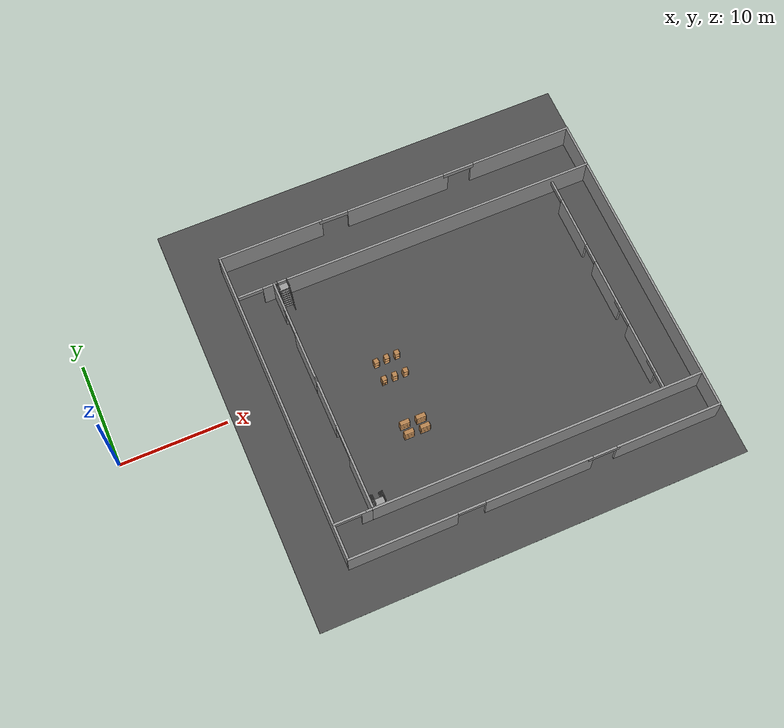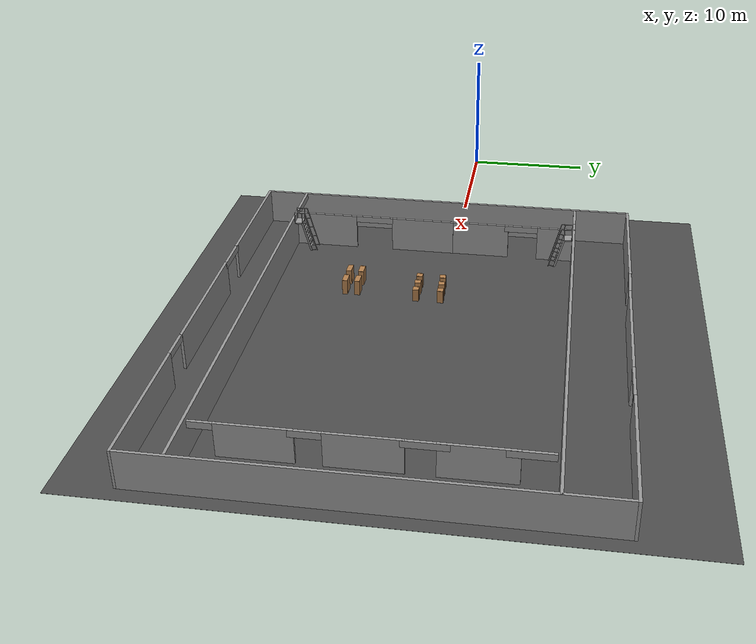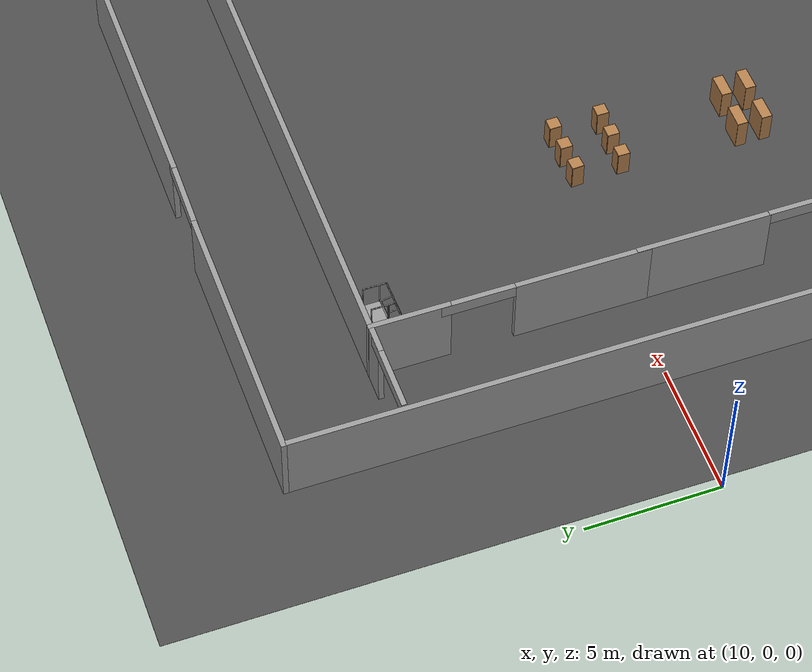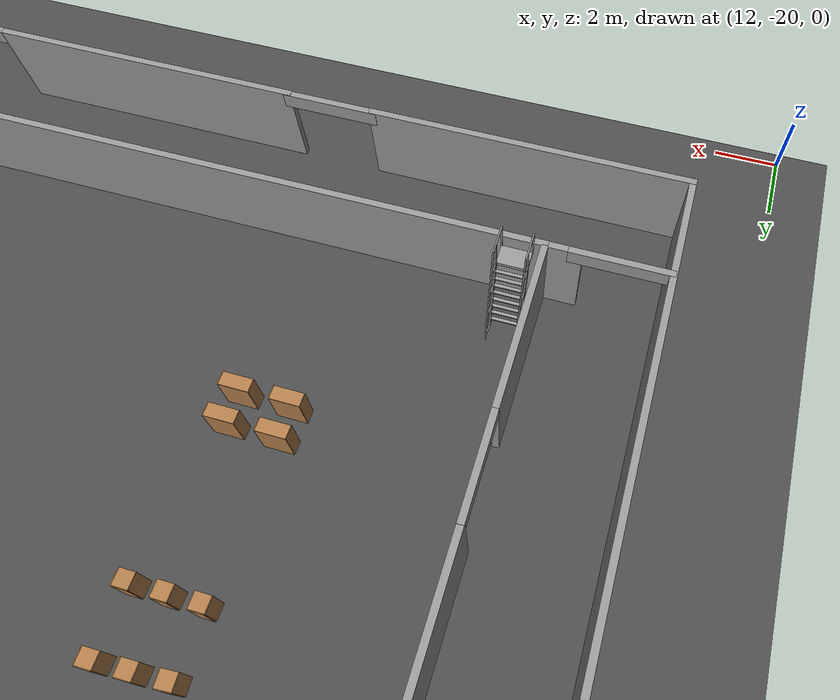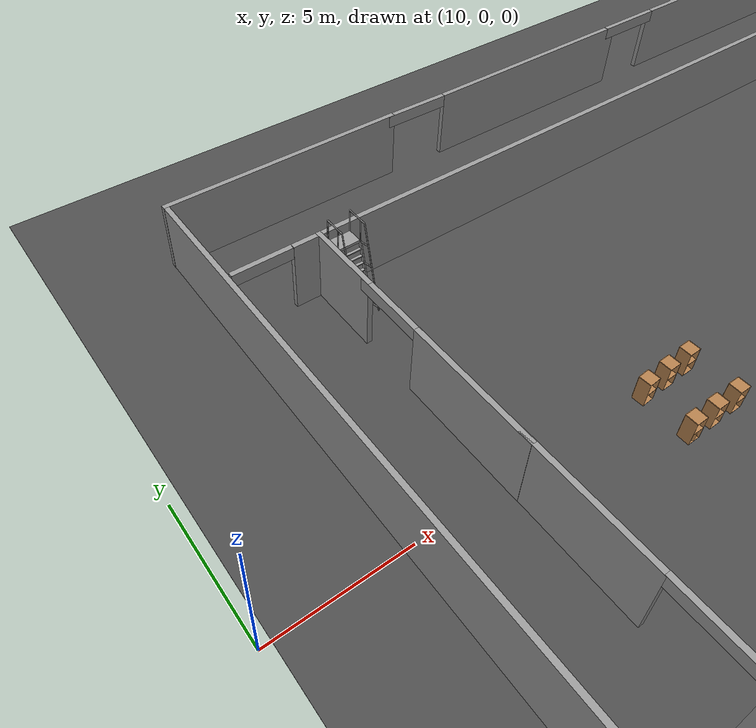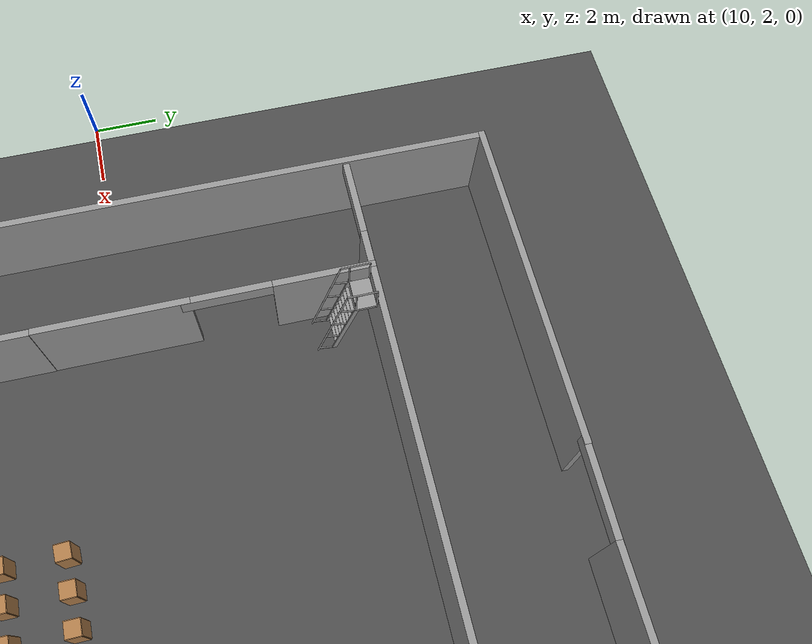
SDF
<sdf version="1.6">
 <world name="default">
  <light name="sun" type="directional">
   <pose>0 0 10 0 -0 0</pose>
   <diffuse>0.8 0.8 0.8 1</diffuse>
   <specular>0.2 0.2 0.2 1</specular>
   <attenuation>
    <range>1000</range>
    <constant>0.9</constant>
    <linear>0.01</linear>
    <quadratic>0.001</quadratic>
   </attenuation>
   <direction>-0.5 0.1 -0.9</direction>
  </light>
  <gravity>0 0 -9.8</gravity>
  <magnetic_field>6e-06 2.3e-05 -4.2e-05</magnetic_field>
  <atmosphere type="adiabatic"/>
  <physics name="default_physics" default="0" type="ode">
   <max_step_size>0.001</max_step_size>
   <real_time_factor>1</real_time_factor>
   <real_time_update_rate>1000</real_time_update_rate>
  </physics>
  <scene><ambient>0.4 0.4 0.4 1</ambient><background>0.7 0.7 0.7 1</background><shadows>1</shadows></scene>
  <audio><device>default</device></audio>
  <spherical_coordinates>
   <surface_model>EARTH_WGS84</surface_model>
   <latitude_deg>0</latitude_deg>
   <longitude_deg>0</longitude_deg>
   <elevation>0</elevation>
   <heading_deg>0</heading_deg>
  </spherical_coordinates>
  <model name="bookshelf">
   <static>1</static>
   <link name="link">
    <inertial><mass>1</mass></inertial>
    <collision name="back">
     <pose>0 0.005 0.6 0 -0 0</pose>
     <geometry><box><size>0.9 0.01 1.2</size></box></geometry>
    </collision>
    <visual name="visual1">
     <pose>0 0.005 0.6 0 -0 0</pose>
     <geometry><box><size>0.9 0.01 1.2</size></box></geometry>
     <material>
      <script><uri>file://media/materials/scripts/gazebo.material</uri><name>Gazebo/Wood</name></script>
     </material>
    </visual>
    <collision name="left_side">
     <pose>0.45 -0.195 0.6 0 -0 0</pose>
     <geometry><box><size>0.02 0.4 1.2</size></box></geometry>
    </collision>
    <visual name="visual2">
     <pose>0.45 -0.195 0.6 0 -0 0</pose>
     <geometry><box><size>0.02 0.4 1.2</size></box></geometry>
     <material>
      <script><uri>file://media/materials/scripts/gazebo.material</uri><name>Gazebo/Wood</name></script>
     </material>
    </visual>
    <collision name="right_side">
     <pose>-0.45 -0.195 0.6 0 -0 0</pose>
     <geometry><box><size>0.02 0.4 1.2</size></box></geometry>
    </collision>
    <visual name="visual3">
     <pose>-0.45 -0.195 0.6 0 -0 0</pose>
     <geometry><box><size>0.02 0.4 1.2</size></box></geometry>
     <material>
      <script><uri>file://media/materials/scripts/gazebo.material</uri><name>Gazebo/Wood</name></script>
     </material>
    </visual>
    <collision name="bottom">
     <pose>0 -0.195 0.03 0 -0 0</pose>
     <geometry><box><size>0.88 0.4 0.06</size></box></geometry>
    </collision>
    <visual name="visual4">
     <pose>0 -0.195 0.03 0 -0 0</pose>
     <geometry><box><size>0.88 0.4 0.06</size></box></geometry>
     <material>
      <script><uri>file://media/materials/scripts/gazebo.material</uri><name>Gazebo/Wood</name></script>
     </material>
    </visual>
    <collision name="top">
     <pose>0 -0.195 1.19 0 -0 0</pose>
     <geometry><box><size>0.88 0.4 0.02</size></box></geometry>
    </collision>
    <visual name="visual5">
     <pose>0 -0.195 1.19 0 -0 0</pose>
     <geometry><box><size>0.88 0.4 0.02</size></box></geometry>
     <material>
      <script><uri>file://media/materials/scripts/gazebo.material</uri><name>Gazebo/Wood</name></script>
     </material>
    </visual>
    <collision name="low_shelf">
     <pose>0 -0.195 0.43 0 -0 0</pose>
     <geometry><box><size>0.88 0.4 0.02</size></box></geometry>
    </collision>
    <visual name="visual6">
     <pose>0 -0.195 0.43 0 -0 0</pose>
     <geometry><box><size>0.88 0.4 0.02</size></box></geometry>
     <material>
      <script><uri>file://media/materials/scripts/gazebo.material</uri><name>Gazebo/Wood</name></script>
     </material>
    </visual>
    <collision name="high_shelf">
     <pose>0 -0.195 0.8 0 -0 0</pose>
     <geometry><box><size>0.88 0.4 0.02</size></box></geometry>
    </collision>
    <visual name="visual7">
     <pose>0 -0.195 0.8 0 -0 0</pose>
     <geometry><box><size>0.88 0.4 0.02</size></box></geometry>
     <material>
      <script><uri>file://media/materials/scripts/gazebo.material</uri><name>Gazebo/Wood</name></script>
     </material>
    </visual>
   </link>
   <pose>24 -6.34826 0 0 -0 0</pose>
  </model>
  <model name="bookshelf_0">
   <static>1</static>
   <link name="link">
    <inertial><mass>1</mass></inertial>
    <collision name="back">
     <pose>0 0.005 0.6 0 -0 0</pose>
     <geometry><box><size>0.9 0.01 1.2</size></box></geometry>
    </collision>
    <visual name="visual1">
     <pose>0 0.005 0.6 0 -0 0</pose>
     <geometry><box><size>0.9 0.01 1.2</size></box></geometry>
     <material>
      <script><uri>file://media/materials/scripts/gazebo.material</uri><name>Gazebo/Wood</name></script>
     </material>
    </visual>
    <collision name="left_side">
     <pose>0.45 -0.195 0.6 0 -0 0</pose>
     <geometry><box><size>0.02 0.4 1.2</size></box></geometry>
    </collision>
    <visual name="visual2">
     <pose>0.45 -0.195 0.6 0 -0 0</pose>
     <geometry><box><size>0.02 0.4 1.2</size></box></geometry>
     <material>
      <script><uri>file://media/materials/scripts/gazebo.material</uri><name>Gazebo/Wood</name></script>
     </material>
    </visual>
    <collision name="right_side">
     <pose>-0.45 -0.195 0.6 0 -0 0</pose>
     <geometry><box><size>0.02 0.4 1.2</size></box></geometry>
    </collision>
    <visual name="visual3">
     <pose>-0.45 -0.195 0.6 0 -0 0</pose>
     <geometry><box><size>0.02 0.4 1.2</size></box></geometry>
     <material>
      <script><uri>file://media/materials/scripts/gazebo.material</uri><name>Gazebo/Wood</name></script>
     </material>
    </visual>
    <collision name="bottom">
     <pose>0 -0.195 0.03 0 -0 0</pose>
     <geometry><box><size>0.88 0.4 0.06</size></box></geometry>
    </collision>
    <visual name="visual4">
     <pose>0 -0.195 0.03 0 -0 0</pose>
     <geometry><box><size>0.88 0.4 0.06</size></box></geometry>
     <material>
      <script><uri>file://media/materials/scripts/gazebo.material</uri><name>Gazebo/Wood</name></script>
     </material>
    </visual>
    <collision name="top">
     <pose>0 -0.195 1.19 0 -0 0</pose>
     <geometry><box><size>0.88 0.4 0.02</size></box></geometry>
    </collision>
    <visual name="visual5">
     <pose>0 -0.195 1.19 0 -0 0</pose>
     <geometry><box><size>0.88 0.4 0.02</size></box></geometry>
     <material>
      <script><uri>file://media/materials/scripts/gazebo.material</uri><name>Gazebo/Wood</name></script>
     </material>
    </visual>
    <collision name="low_shelf">
     <pose>0 -0.195 0.43 0 -0 0</pose>
     <geometry><box><size>0.88 0.4 0.02</size></box></geometry>
    </collision>
    <visual name="visual6">
     <pose>0 -0.195 0.43 0 -0 0</pose>
     <geometry><box><size>0.88 0.4 0.02</size></box></geometry>
     <material>
      <script><uri>file://media/materials/scripts/gazebo.material</uri><name>Gazebo/Wood</name></script>
     </material>
    </visual>
    <collision name="high_shelf">
     <pose>0 -0.195 0.8 0 -0 0</pose>
     <geometry><box><size>0.88 0.4 0.02</size></box></geometry>
    </collision>
    <visual name="visual7">
     <pose>0 -0.195 0.8 0 -0 0</pose>
     <geometry><box><size>0.88 0.4 0.02</size></box></geometry>
     <material>
      <script><uri>file://media/materials/scripts/gazebo.material</uri><name>Gazebo/Wood</name></script>
     </material>
    </visual>
   </link>
   <pose>24 -7.29732 0 0 -0 0</pose>
  </model>
  <model name="bookshelf_4">
   <static>1</static>
   <link name="link">
    <inertial><mass>1</mass></inertial>
    <collision name="back">
     <pose>0 0.005 0.6 0 -0 0</pose>
     <geometry><box><size>0.9 0.01 1.2</size></box></geometry>
    </collision>
    <visual name="visual1">
     <pose>0 0.005 0.6 0 -0 0</pose>
     <geometry><box><size>0.9 0.01 1.2</size></box></geometry>
     <material>
      <script><uri>file://media/materials/scripts/gazebo.material</uri><name>Gazebo/Wood</name></script>
     </material>
    </visual>
    <collision name="left_side">
     <pose>0.45 -0.195 0.6 0 -0 0</pose>
     <geometry><box><size>0.02 0.4 1.2</size></box></geometry>
    </collision>
    <visual name="visual2">
     <pose>0.45 -0.195 0.6 0 -0 0</pose>
     <geometry><box><size>0.02 0.4 1.2</size></box></geometry>
     <material>
      <script><uri>file://media/materials/scripts/gazebo.material</uri><name>Gazebo/Wood</name></script>
     </material>
    </visual>
    <collision name="right_side">
     <pose>-0.45 -0.195 0.6 0 -0 0</pose>
     <geometry><box><size>0.02 0.4 1.2</size></box></geometry>
    </collision>
    <visual name="visual3">
     <pose>-0.45 -0.195 0.6 0 -0 0</pose>
     <geometry><box><size>0.02 0.4 1.2</size></box></geometry>
     <material>
      <script><uri>file://media/materials/scripts/gazebo.material</uri><name>Gazebo/Wood</name></script>
     </material>
    </visual>
    <collision name="bottom">
     <pose>0 -0.195 0.03 0 -0 0</pose>
     <geometry><box><size>0.88 0.4 0.06</size></box></geometry>
    </collision>
    <visual name="visual4">
     <pose>0 -0.195 0.03 0 -0 0</pose>
     <geometry><box><size>0.88 0.4 0.06</size></box></geometry>
     <material>
      <script><uri>file://media/materials/scripts/gazebo.material</uri><name>Gazebo/Wood</name></script>
     </material>
    </visual>
    <collision name="top">
     <pose>0 -0.195 1.19 0 -0 0</pose>
     <geometry><box><size>0.88 0.4 0.02</size></box></geometry>
    </collision>
    <visual name="visual5">
     <pose>0 -0.195 1.19 0 -0 0</pose>
     <geometry><box><size>0.88 0.4 0.02</size></box></geometry>
     <material>
      <script><uri>file://media/materials/scripts/gazebo.material</uri><name>Gazebo/Wood</name></script>
     </material>
    </visual>
    <collision name="low_shelf">
     <pose>0 -0.195 0.43 0 -0 0</pose>
     <geometry><box><size>0.88 0.4 0.02</size></box></geometry>
    </collision>
    <visual name="visual6">
     <pose>0 -0.195 0.43 0 -0 0</pose>
     <geometry><box><size>0.88 0.4 0.02</size></box></geometry>
     <material>
      <script><uri>file://media/materials/scripts/gazebo.material</uri><name>Gazebo/Wood</name></script>
     </material>
    </visual>
    <collision name="high_shelf">
     <pose>0 -0.195 0.8 0 -0 0</pose>
     <geometry><box><size>0.88 0.4 0.02</size></box></geometry>
    </collision>
    <visual name="visual7">
     <pose>0 -0.195 0.8 0 -0 0</pose>
     <geometry><box><size>0.88 0.4 0.02</size></box></geometry>
     <material>
      <script><uri>file://media/materials/scripts/gazebo.material</uri><name>Gazebo/Wood</name></script>
     </material>
    </visual>
   </link>
   <pose>25.4994 -7.31169 0 0 -0 0</pose>
  </model>
  <model name="bookshelf_7">
   <static>1</static>
   <link name="link">
    <inertial><mass>1</mass></inertial>
    <collision name="back">
     <pose>0 0.005 0.6 0 -0 0</pose>
     <geometry><box><size>0.9 0.01 1.2</size></box></geometry>
    </collision>
    <visual name="visual1">
     <pose>0 0.005 0.6 0 -0 0</pose>
     <geometry><box><size>0.9 0.01 1.2</size></box></geometry>
     <material>
      <script><uri>file://media/materials/scripts/gazebo.material</uri><name>Gazebo/Wood</name></script>
     </material>
    </visual>
    <collision name="left_side">
     <pose>0.45 -0.195 0.6 0 -0 0</pose>
     <geometry><box><size>0.02 0.4 1.2</size></box></geometry>
    </collision>
    <visual name="visual2">
     <pose>0.45 -0.195 0.6 0 -0 0</pose>
     <geometry><box><size>0.02 0.4 1.2</size></box></geometry>
     <material>
      <script><uri>file://media/materials/scripts/gazebo.material</uri><name>Gazebo/Wood</name></script>
     </material>
    </visual>
    <collision name="right_side">
     <pose>-0.45 -0.195 0.6 0 -0 0</pose>
     <geometry><box><size>0.02 0.4 1.2</size></box></geometry>
    </collision>
    <visual name="visual3">
     <pose>-0.45 -0.195 0.6 0 -0 0</pose>
     <geometry><box><size>0.02 0.4 1.2</size></box></geometry>
     <material>
      <script><uri>file://media/materials/scripts/gazebo.material</uri><name>Gazebo/Wood</name></script>
     </material>
    </visual>
    <collision name="bottom">
     <pose>0 -0.195 0.03 0 -0 0</pose>
     <geometry><box><size>0.88 0.4 0.06</size></box></geometry>
    </collision>
    <visual name="visual4">
     <pose>0 -0.195 0.03 0 -0 0</pose>
     <geometry><box><size>0.88 0.4 0.06</size></box></geometry>
     <material>
      <script><uri>file://media/materials/scripts/gazebo.material</uri><name>Gazebo/Wood</name></script>
     </material>
    </visual>
    <collision name="top">
     <pose>0 -0.195 1.19 0 -0 0</pose>
     <geometry><box><size>0.88 0.4 0.02</size></box></geometry>
    </collision>
    <visual name="visual5">
     <pose>0 -0.195 1.19 0 -0 0</pose>
     <geometry><box><size>0.88 0.4 0.02</size></box></geometry>
     <material>
      <script><uri>file://media/materials/scripts/gazebo.material</uri><name>Gazebo/Wood</name></script>
     </material>
    </visual>
    <collision name="low_shelf">
     <pose>0 -0.195 0.43 0 -0 0</pose>
     <geometry><box><size>0.88 0.4 0.02</size></box></geometry>
    </collision>
    <visual name="visual6">
     <pose>0 -0.195 0.43 0 -0 0</pose>
     <geometry><box><size>0.88 0.4 0.02</size></box></geometry>
     <material>
      <script><uri>file://media/materials/scripts/gazebo.material</uri><name>Gazebo/Wood</name></script>
     </material>
    </visual>
    <collision name="high_shelf">
     <pose>0 -0.195 0.8 0 -0 0</pose>
     <geometry><box><size>0.88 0.4 0.02</size></box></geometry>
    </collision>
    <visual name="visual7">
     <pose>0 -0.195 0.8 0 -0 0</pose>
     <geometry><box><size>0.88 0.4 0.02</size></box></geometry>
     <material>
      <script><uri>file://media/materials/scripts/gazebo.material</uri><name>Gazebo/Wood</name></script>
     </material>
    </visual>
   </link>
   <pose>25.5 -6.37044 0 0 -0 0</pose>
  </model>
  <model name="cabinet">
   <static>1</static>
   <link name="cabinet_bottom_plate">
    <inertial>
     <pose>0 0 -1 0 -0 0</pose>
     <inertia><ixx>2.05</ixx><ixy>0</ixy><ixz>0</ixz><iyy>2.05</iyy><iyz>0</iyz><izz>2.05</izz></inertia>
     <mass>25</mass>
    </inertial>
    <collision name="cabinet_bottom_plate_geom">
     <pose>0 0 0.01 0 -0 0</pose>
     <geometry><box><size>0.45 0.45 0.02</size></box></geometry>
    </collision>
    <visual name="cabinet_bottom_plate_geom_visual">
     <pose>0 0 0.01 0 -0 0</pose>
     <geometry><box><size>0.45 0.45 0.02</size></box></geometry>
     <material>
      <script><uri>file://media/materials/scripts/gazebo.material</uri><name>Gazebo/Wood</name></script>
     </material>
    </visual>
    <collision name="cabinet_bottom_plate_geom_cabinet_back_plate">
     <pose>0.235 0 0.51 0 -0 0</pose>
     <geometry><box><size>0.02 0.45 1.02</size></box></geometry>
    </collision>
    <visual name="cabinet_bottom_plate_geom_cabinet_back_plate_visual">
     <pose>0.235 0 0.51 0 -0 0</pose>
     <geometry><box><size>0.02 0.45 1.02</size></box></geometry>
     <material>
      <script><uri>file://media/materials/scripts/gazebo.material</uri><name>Gazebo/Wood</name></script>
     </material>
    </visual>
    <collision name="cabinet_bottom_plate_geom_cabinet_left_plate">
     <pose>0 0.235 0.51 0 -0 0</pose>
     <geometry><box><size>0.45 0.02 1.02</size></box></geometry>
    </collision>
    <visual name="cabinet_bottom_plate_geom_cabinet_left_plate_visual">
     <pose>0 0.235 0.51 0 -0 0</pose>
     <geometry><box><size>0.45 0.02 1.02</size></box></geometry>
     <material>
      <script><uri>file://media/materials/scripts/gazebo.material</uri><name>Gazebo/Wood</name></script>
     </material>
    </visual>
    <collision name="cabinet_bottom_plate_geom_cabinet_middle_plate">
     <pose>0 0 0.51 0 -0 0</pose>
     <geometry><box><size>0.45 0.45 0.02</size></box></geometry>
    </collision>
    <visual name="cabinet_bottom_plate_geom_cabinet_middle_plate_visual">
     <pose>0 0 0.51 0 -0 0</pose>
     <geometry><box><size>0.45 0.45 0.02</size></box></geometry>
     <material>
      <script><uri>file://media/materials/scripts/gazebo.material</uri><name>Gazebo/Wood</name></script>
     </material>
    </visual>
    <collision name="cabinet_bottom_plate_geom_cabinet_right_plate">
     <pose>0 -0.235 0.51 0 -0 0</pose>
     <geometry><box><size>0.45 0.02 1.02</size></box></geometry>
    </collision>
    <visual name="cabinet_bottom_plate_geom_cabinet_right_plate_visual">
     <pose>0 -0.235 0.51 0 -0 0</pose>
     <geometry><box><size>0.45 0.02 1.02</size></box></geometry>
     <material>
      <script><uri>file://media/materials/scripts/gazebo.material</uri><name>Gazebo/Wood</name></script>
     </material>
    </visual>
    <collision name="cabinet_bottom_plate_geom_cabinet_top_plate">
     <pose>0 0 1.01 0 -0 0</pose>
     <geometry><box><size>0.45 0.45 0.02</size></box></geometry>
    </collision>
    <visual name="cabinet_bottom_plate_geom_cabinet_top_plate_visual">
     <pose>0 0 1.01 0 -0 0</pose>
     <geometry><box><size>0.45 0.45 0.02</size></box></geometry>
     <material>
      <script><uri>file://media/materials/scripts/gazebo.material</uri><name>Gazebo/Wood</name></script>
     </material>
    </visual>
   </link>
   <pose>24 -2 0 0 -0 1.57</pose>
  </model>
  <model name="cabinet_0">
   <static>1</static>
   <link name="cabinet_bottom_plate">
    <inertial>
     <pose>0 0 -1 0 -0 0</pose>
     <inertia><ixx>2.05</ixx><ixy>0</ixy><ixz>0</ixz><iyy>2.05</iyy><iyz>0</iyz><izz>2.05</izz></inertia>
     <mass>25</mass>
    </inertial>
    <collision name="cabinet_bottom_plate_geom">
     <pose>0 0 0.01 0 -0 0</pose>
     <geometry><box><size>0.45 0.45 0.02</size></box></geometry>
    </collision>
    <visual name="cabinet_bottom_plate_geom_visual">
     <pose>0 0 0.01 0 -0 0</pose>
     <geometry><box><size>0.45 0.45 0.02</size></box></geometry>
     <material>
      <script><uri>file://media/materials/scripts/gazebo.material</uri><name>Gazebo/Wood</name></script>
     </material>
    </visual>
    <collision name="cabinet_bottom_plate_geom_cabinet_back_plate">
     <pose>0.235 0 0.51 0 -0 0</pose>
     <geometry><box><size>0.02 0.45 1.02</size></box></geometry>
    </collision>
    <visual name="cabinet_bottom_plate_geom_cabinet_back_plate_visual">
     <pose>0.235 0 0.51 0 -0 0</pose>
     <geometry><box><size>0.02 0.45 1.02</size></box></geometry>
     <material>
      <script><uri>file://media/materials/scripts/gazebo.material</uri><name>Gazebo/Wood</name></script>
     </material>
    </visual>
    <collision name="cabinet_bottom_plate_geom_cabinet_left_plate">
     <pose>0 0.235 0.51 0 -0 0</pose>
     <geometry><box><size>0.45 0.02 1.02</size></box></geometry>
    </collision>
    <visual name="cabinet_bottom_plate_geom_cabinet_left_plate_visual">
     <pose>0 0.235 0.51 0 -0 0</pose>
     <geometry><box><size>0.45 0.02 1.02</size></box></geometry>
     <material>
      <script><uri>file://media/materials/scripts/gazebo.material</uri><name>Gazebo/Wood</name></script>
     </material>
    </visual>
    <collision name="cabinet_bottom_plate_geom_cabinet_middle_plate">
     <pose>0 0 0.51 0 -0 0</pose>
     <geometry><box><size>0.45 0.45 0.02</size></box></geometry>
    </collision>
    <visual name="cabinet_bottom_plate_geom_cabinet_middle_plate_visual">
     <pose>0 0 0.51 0 -0 0</pose>
     <geometry><box><size>0.45 0.45 0.02</size></box></geometry>
     <material>
      <script><uri>file://media/materials/scripts/gazebo.material</uri><name>Gazebo/Wood</name></script>
     </material>
    </visual>
    <collision name="cabinet_bottom_plate_geom_cabinet_right_plate">
     <pose>0 -0.235 0.51 0 -0 0</pose>
     <geometry><box><size>0.45 0.02 1.02</size></box></geometry>
    </collision>
    <visual name="cabinet_bottom_plate_geom_cabinet_right_plate_visual">
     <pose>0 -0.235 0.51 0 -0 0</pose>
     <geometry><box><size>0.45 0.02 1.02</size></box></geometry>
     <material>
      <script><uri>file://media/materials/scripts/gazebo.material</uri><name>Gazebo/Wood</name></script>
     </material>
    </visual>
    <collision name="cabinet_bottom_plate_geom_cabinet_top_plate">
     <pose>0 0 1.01 0 -0 0</pose>
     <geometry><box><size>0.45 0.45 0.02</size></box></geometry>
    </collision>
    <visual name="cabinet_bottom_plate_geom_cabinet_top_plate_visual">
     <pose>0 0 1.01 0 -0 0</pose>
     <geometry><box><size>0.45 0.45 0.02</size></box></geometry>
     <material>
      <script><uri>file://media/materials/scripts/gazebo.material</uri><name>Gazebo/Wood</name></script>
     </material>
    </visual>
   </link>
   <pose>24 -0.211293 0 0 -0 1.63157</pose>
  </model>
  <model name="cabinet_1">
   <static>1</static>
   <link name="cabinet_bottom_plate">
    <inertial>
     <pose>0 0 -1 0 -0 0</pose>
     <inertia><ixx>2.05</ixx><ixy>0</ixy><ixz>0</ixz><iyy>2.05</iyy><iyz>0</iyz><izz>2.05</izz></inertia>
     <mass>25</mass>
    </inertial>
    <collision name="cabinet_bottom_plate_geom">
     <pose>0 0 0.01 0 -0 0</pose>
     <geometry><box><size>0.45 0.45 0.02</size></box></geometry>
    </collision>
    <visual name="cabinet_bottom_plate_geom_visual">
     <pose>0 0 0.01 0 -0 0</pose>
     <geometry><box><size>0.45 0.45 0.02</size></box></geometry>
     <material>
      <script><uri>file://media/materials/scripts/gazebo.material</uri><name>Gazebo/Wood</name></script>
     </material>
    </visual>
    <collision name="cabinet_bottom_plate_geom_cabinet_back_plate">
     <pose>0.235 0 0.51 0 -0 0</pose>
     <geometry><box><size>0.02 0.45 1.02</size></box></geometry>
    </collision>
    <visual name="cabinet_bottom_plate_geom_cabinet_back_plate_visual">
     <pose>0.235 0 0.51 0 -0 0</pose>
     <geometry><box><size>0.02 0.45 1.02</size></box></geometry>
     <material>
      <script><uri>file://media/materials/scripts/gazebo.material</uri><name>Gazebo/Wood</name></script>
     </material>
    </visual>
    <collision name="cabinet_bottom_plate_geom_cabinet_left_plate">
     <pose>0 0.235 0.51 0 -0 0</pose>
     <geometry><box><size>0.45 0.02 1.02</size></box></geometry>
    </collision>
    <visual name="cabinet_bottom_plate_geom_cabinet_left_plate_visual">
     <pose>0 0.235 0.51 0 -0 0</pose>
     <geometry><box><size>0.45 0.02 1.02</size></box></geometry>
     <material>
      <script><uri>file://media/materials/scripts/gazebo.material</uri><name>Gazebo/Wood</name></script>
     </material>
    </visual>
    <collision name="cabinet_bottom_plate_geom_cabinet_middle_plate">
     <pose>0 0 0.51 0 -0 0</pose>
     <geometry><box><size>0.45 0.45 0.02</size></box></geometry>
    </collision>
    <visual name="cabinet_bottom_plate_geom_cabinet_middle_plate_visual">
     <pose>0 0 0.51 0 -0 0</pose>
     <geometry><box><size>0.45 0.45 0.02</size></box></geometry>
     <material>
      <script><uri>file://media/materials/scripts/gazebo.material</uri><name>Gazebo/Wood</name></script>
     </material>
    </visual>
    <collision name="cabinet_bottom_plate_geom_cabinet_right_plate">
     <pose>0 -0.235 0.51 0 -0 0</pose>
     <geometry><box><size>0.45 0.02 1.02</size></box></geometry>
    </collision>
    <visual name="cabinet_bottom_plate_geom_cabinet_right_plate_visual">
     <pose>0 -0.235 0.51 0 -0 0</pose>
     <geometry><box><size>0.45 0.02 1.02</size></box></geometry>
     <material>
      <script><uri>file://media/materials/scripts/gazebo.material</uri><name>Gazebo/Wood</name></script>
     </material>
    </visual>
    <collision name="cabinet_bottom_plate_geom_cabinet_top_plate">
     <pose>0 0 1.01 0 -0 0</pose>
     <geometry><box><size>0.45 0.45 0.02</size></box></geometry>
    </collision>
    <visual name="cabinet_bottom_plate_geom_cabinet_top_plate_visual">
     <pose>0 0 1.01 0 -0 0</pose>
     <geometry><box><size>0.45 0.45 0.02</size></box></geometry>
     <material>
      <script><uri>file://media/materials/scripts/gazebo.material</uri><name>Gazebo/Wood</name></script>
     </material>
    </visual>
   </link>
   <pose>25 -0.169358 0 0 -0 1.58885</pose>
  </model>
  <model name="cabinet_2">
   <static>1</static>
   <link name="cabinet_bottom_plate">
    <inertial>
     <pose>0 0 -1 0 -0 0</pose>
     <inertia><ixx>2.05</ixx><ixy>0</ixy><ixz>0</ixz><iyy>2.05</iyy><iyz>0</iyz><izz>2.05</izz></inertia>
     <mass>25</mass>
    </inertial>
    <collision name="cabinet_bottom_plate_geom">
     <pose>0 0 0.01 0 -0 0</pose>
     <geometry><box><size>0.45 0.45 0.02</size></box></geometry>
    </collision>
    <visual name="cabinet_bottom_plate_geom_visual">
     <pose>0 0 0.01 0 -0 0</pose>
     <geometry><box><size>0.45 0.45 0.02</size></box></geometry>
     <material>
      <script><uri>file://media/materials/scripts/gazebo.material</uri><name>Gazebo/Wood</name></script>
     </material>
    </visual>
    <collision name="cabinet_bottom_plate_geom_cabinet_back_plate">
     <pose>0.235 0 0.51 0 -0 0</pose>
     <geometry><box><size>0.02 0.45 1.02</size></box></geometry>
    </collision>
    <visual name="cabinet_bottom_plate_geom_cabinet_back_plate_visual">
     <pose>0.235 0 0.51 0 -0 0</pose>
     <geometry><box><size>0.02 0.45 1.02</size></box></geometry>
     <material>
      <script><uri>file://media/materials/scripts/gazebo.material</uri><name>Gazebo/Wood</name></script>
     </material>
    </visual>
    <collision name="cabinet_bottom_plate_geom_cabinet_left_plate">
     <pose>0 0.235 0.51 0 -0 0</pose>
     <geometry><box><size>0.45 0.02 1.02</size></box></geometry>
    </collision>
    <visual name="cabinet_bottom_plate_geom_cabinet_left_plate_visual">
     <pose>0 0.235 0.51 0 -0 0</pose>
     <geometry><box><size>0.45 0.02 1.02</size></box></geometry>
     <material>
      <script><uri>file://media/materials/scripts/gazebo.material</uri><name>Gazebo/Wood</name></script>
     </material>
    </visual>
    <collision name="cabinet_bottom_plate_geom_cabinet_middle_plate">
     <pose>0 0 0.51 0 -0 0</pose>
     <geometry><box><size>0.45 0.45 0.02</size></box></geometry>
    </collision>
    <visual name="cabinet_bottom_plate_geom_cabinet_middle_plate_visual">
     <pose>0 0 0.51 0 -0 0</pose>
     <geometry><box><size>0.45 0.45 0.02</size></box></geometry>
     <material>
      <script><uri>file://media/materials/scripts/gazebo.material</uri><name>Gazebo/Wood</name></script>
     </material>
    </visual>
    <collision name="cabinet_bottom_plate_geom_cabinet_right_plate">
     <pose>0 -0.235 0.51 0 -0 0</pose>
     <geometry><box><size>0.45 0.02 1.02</size></box></geometry>
    </collision>
    <visual name="cabinet_bottom_plate_geom_cabinet_right_plate_visual">
     <pose>0 -0.235 0.51 0 -0 0</pose>
     <geometry><box><size>0.45 0.02 1.02</size></box></geometry>
     <material>
      <script><uri>file://media/materials/scripts/gazebo.material</uri><name>Gazebo/Wood</name></script>
     </material>
    </visual>
    <collision name="cabinet_bottom_plate_geom_cabinet_top_plate">
     <pose>0 0 1.01 0 -0 0</pose>
     <geometry><box><size>0.45 0.45 0.02</size></box></geometry>
    </collision>
    <visual name="cabinet_bottom_plate_geom_cabinet_top_plate_visual">
     <pose>0 0 1.01 0 -0 0</pose>
     <geometry><box><size>0.45 0.45 0.02</size></box></geometry>
     <material>
      <script><uri>file://media/materials/scripts/gazebo.material</uri><name>Gazebo/Wood</name></script>
     </material>
    </visual>
   </link>
   <pose>25 -2 0 0 -0 1.57</pose>
  </model>
  <model name="cabinet_3">
   <static>1</static>
   <link name="cabinet_bottom_plate">
    <inertial>
     <pose>0 0 -1 0 -0 0</pose>
     <inertia><ixx>2.05</ixx><ixy>0</ixy><ixz>0</ixz><iyy>2.05</iyy><iyz>0</iyz><izz>2.05</izz></inertia>
     <mass>25</mass>
    </inertial>
    <collision name="cabinet_bottom_plate_geom">
     <pose>0 0 0.01 0 -0 0</pose>
     <geometry><box><size>0.45 0.45 0.02</size></box></geometry>
    </collision>
    <visual name="cabinet_bottom_plate_geom_visual">
     <pose>0 0 0.01 0 -0 0</pose>
     <geometry><box><size>0.45 0.45 0.02</size></box></geometry>
     <material>
      <script><uri>file://media/materials/scripts/gazebo.material</uri><name>Gazebo/Wood</name></script>
     </material>
    </visual>
    <collision name="cabinet_bottom_plate_geom_cabinet_back_plate">
     <pose>0.235 0 0.51 0 -0 0</pose>
     <geometry><box><size>0.02 0.45 1.02</size></box></geometry>
    </collision>
    <visual name="cabinet_bottom_plate_geom_cabinet_back_plate_visual">
     <pose>0.235 0 0.51 0 -0 0</pose>
     <geometry><box><size>0.02 0.45 1.02</size></box></geometry>
     <material>
      <script><uri>file://media/materials/scripts/gazebo.material</uri><name>Gazebo/Wood</name></script>
     </material>
    </visual>
    <collision name="cabinet_bottom_plate_geom_cabinet_left_plate">
     <pose>0 0.235 0.51 0 -0 0</pose>
     <geometry><box><size>0.45 0.02 1.02</size></box></geometry>
    </collision>
    <visual name="cabinet_bottom_plate_geom_cabinet_left_plate_visual">
     <pose>0 0.235 0.51 0 -0 0</pose>
     <geometry><box><size>0.45 0.02 1.02</size></box></geometry>
     <material>
      <script><uri>file://media/materials/scripts/gazebo.material</uri><name>Gazebo/Wood</name></script>
     </material>
    </visual>
    <collision name="cabinet_bottom_plate_geom_cabinet_middle_plate">
     <pose>0 0 0.51 0 -0 0</pose>
     <geometry><box><size>0.45 0.45 0.02</size></box></geometry>
    </collision>
    <visual name="cabinet_bottom_plate_geom_cabinet_middle_plate_visual">
     <pose>0 0 0.51 0 -0 0</pose>
     <geometry><box><size>0.45 0.45 0.02</size></box></geometry>
     <material>
      <script><uri>file://media/materials/scripts/gazebo.material</uri><name>Gazebo/Wood</name></script>
     </material>
    </visual>
    <collision name="cabinet_bottom_plate_geom_cabinet_right_plate">
     <pose>0 -0.235 0.51 0 -0 0</pose>
     <geometry><box><size>0.45 0.02 1.02</size></box></geometry>
    </collision>
    <visual name="cabinet_bottom_plate_geom_cabinet_right_plate_visual">
     <pose>0 -0.235 0.51 0 -0 0</pose>
     <geometry><box><size>0.45 0.02 1.02</size></box></geometry>
     <material>
      <script><uri>file://media/materials/scripts/gazebo.material</uri><name>Gazebo/Wood</name></script>
     </material>
    </visual>
    <collision name="cabinet_bottom_plate_geom_cabinet_top_plate">
     <pose>0 0 1.01 0 -0 0</pose>
     <geometry><box><size>0.45 0.45 0.02</size></box></geometry>
    </collision>
    <visual name="cabinet_bottom_plate_geom_cabinet_top_plate_visual">
     <pose>0 0 1.01 0 -0 0</pose>
     <geometry><box><size>0.45 0.45 0.02</size></box></geometry>
     <material>
      <script><uri>file://media/materials/scripts/gazebo.material</uri><name>Gazebo/Wood</name></script>
     </material>
    </visual>
   </link>
   <pose>26 -0.139945 0 0 -0 1.58292</pose>
  </model>
  <model name="cabinet_4">
   <static>1</static>
   <link name="cabinet_bottom_plate">
    <inertial>
     <pose>0 0 -1 0 -0 0</pose>
     <inertia><ixx>2.05</ixx><ixy>0</ixy><ixz>0</ixz><iyy>2.05</iyy><iyz>0</iyz><izz>2.05</izz></inertia>
     <mass>25</mass>
    </inertial>
    <collision name="cabinet_bottom_plate_geom">
     <pose>0 0 0.01 0 -0 0</pose>
     <geometry><box><size>0.45 0.45 0.02</size></box></geometry>
    </collision>
    <visual name="cabinet_bottom_plate_geom_visual">
     <pose>0 0 0.01 0 -0 0</pose>
     <geometry><box><size>0.45 0.45 0.02</size></box></geometry>
     <material>
      <script><uri>file://media/materials/scripts/gazebo.material</uri><name>Gazebo/Wood</name></script>
     </material>
    </visual>
    <collision name="cabinet_bottom_plate_geom_cabinet_back_plate">
     <pose>0.235 0 0.51 0 -0 0</pose>
     <geometry><box><size>0.02 0.45 1.02</size></box></geometry>
    </collision>
    <visual name="cabinet_bottom_plate_geom_cabinet_back_plate_visual">
     <pose>0.235 0 0.51 0 -0 0</pose>
     <geometry><box><size>0.02 0.45 1.02</size></box></geometry>
     <material>
      <script><uri>file://media/materials/scripts/gazebo.material</uri><name>Gazebo/Wood</name></script>
     </material>
    </visual>
    <collision name="cabinet_bottom_plate_geom_cabinet_left_plate">
     <pose>0 0.235 0.51 0 -0 0</pose>
     <geometry><box><size>0.45 0.02 1.02</size></box></geometry>
    </collision>
    <visual name="cabinet_bottom_plate_geom_cabinet_left_plate_visual">
     <pose>0 0.235 0.51 0 -0 0</pose>
     <geometry><box><size>0.45 0.02 1.02</size></box></geometry>
     <material>
      <script><uri>file://media/materials/scripts/gazebo.material</uri><name>Gazebo/Wood</name></script>
     </material>
    </visual>
    <collision name="cabinet_bottom_plate_geom_cabinet_middle_plate">
     <pose>0 0 0.51 0 -0 0</pose>
     <geometry><box><size>0.45 0.45 0.02</size></box></geometry>
    </collision>
    <visual name="cabinet_bottom_plate_geom_cabinet_middle_plate_visual">
     <pose>0 0 0.51 0 -0 0</pose>
     <geometry><box><size>0.45 0.45 0.02</size></box></geometry>
     <material>
      <script><uri>file://media/materials/scripts/gazebo.material</uri><name>Gazebo/Wood</name></script>
     </material>
    </visual>
    <collision name="cabinet_bottom_plate_geom_cabinet_right_plate">
     <pose>0 -0.235 0.51 0 -0 0</pose>
     <geometry><box><size>0.45 0.02 1.02</size></box></geometry>
    </collision>
    <visual name="cabinet_bottom_plate_geom_cabinet_right_plate_visual">
     <pose>0 -0.235 0.51 0 -0 0</pose>
     <geometry><box><size>0.45 0.02 1.02</size></box></geometry>
     <material>
      <script><uri>file://media/materials/scripts/gazebo.material</uri><name>Gazebo/Wood</name></script>
     </material>
    </visual>
    <collision name="cabinet_bottom_plate_geom_cabinet_top_plate">
     <pose>0 0 1.01 0 -0 0</pose>
     <geometry><box><size>0.45 0.45 0.02</size></box></geometry>
    </collision>
    <visual name="cabinet_bottom_plate_geom_cabinet_top_plate_visual">
     <pose>0 0 1.01 0 -0 0</pose>
     <geometry><box><size>0.45 0.45 0.02</size></box></geometry>
     <material>
      <script><uri>file://media/materials/scripts/gazebo.material</uri><name>Gazebo/Wood</name></script>
     </material>
    </visual>
   </link>
   <pose>26 -2 0 0.032838 -0.000583 1.57</pose>
  </model>
  <light name="user_directional_light_0" type="directional">
   <pose>-15.226 16.5838 1 0 -0 0</pose>
   <diffuse>0.5 0.5 0.5 1</diffuse>
   <specular>0.1 0.1 0.1 1</specular>
   <direction>0.1 0.1 -0.9</direction>
   <attenuation>
    <range>20</range>
    <constant>0.5</constant>
    <linear>0.01</linear>
    <quadratic>0.001</quadratic>
   </attenuation>
  </light>
  <model name="grey_wall_3">
   <static>1</static>
   <link name="link">
    <pose>0 0 1.4 0 -0 0</pose>
    <collision name="collision"><geometry><box><size>30 0.2 2.8</size></box></geometry></collision>
    <visual name="visual">
     <cast_shadows>0</cast_shadows>
     <geometry><box><size>30 0.2 2.8</size></box></geometry>
     <material>
      <script>
       <uri>model://grey_wall/materials/scripts</uri>
       <uri>model://grey_wall/materials/textures</uri>
       <name>vrc/grey_wall</name>
      </script>
     </material>
    </visual>
   </link>
   <pose>14.7292 -1.22253 0 0 -0 1.57</pose>
  </model>
  <model name="grey_wall_4">
   <static>1</static>
   <link name="link">
    <pose>0 0 1.4 0 -0 0</pose>
    <collision name="collision"><geometry><box><size>30 0.2 2.8</size></box></geometry></collision>
    <visual name="visual">
     <cast_shadows>0</cast_shadows>
     <geometry><box><size>30 0.2 2.8</size></box></geometry>
     <material>
      <script>
       <uri>model://grey_wall/materials/scripts</uri>
       <uri>model://grey_wall/materials/textures</uri>
       <name>vrc/grey_wall</name>
      </script>
     </material>
    </visual>
   </link>
   <pose>49.3131 -1.24144 0 0 -0 1.57</pose>
  </model>
  <model name="grey_wall_5">
   <static>1</static>
   <link name="link">
    <pose>0 0 1.4 0 -0 0</pose>
    <collision name="collision"><geometry><box><size>10 0.2 2.8</size></box></geometry></collision>
    <visual name="visual">
     <cast_shadows>0</cast_shadows>
     <geometry><box><size>10 0.2 2.8</size></box></geometry>
     <material>
      <script>
       <uri>model://grey_wall/materials/scripts</uri>
       <uri>model://grey_wall/materials/textures</uri>
       <name>vrc/grey_wall</name>
      </script>
     </material>
    </visual>
   </link>
   <pose>19.6162 -16.3247 0 0 -0 0</pose>
  </model>
  <model name="grey_wall_6">
   <static>1</static>
   <link name="link">
    <pose>0 0 1.4 0 -0 0</pose>
    <collision name="collision"><geometry><box><size>10 0.2 2.8</size></box></geometry></collision>
    <visual name="visual">
     <cast_shadows>0</cast_shadows>
     <geometry><box><size>10 0.2 2.8</size></box></geometry>
     <material>
      <script>
       <uri>model://grey_wall/materials/scripts</uri>
       <uri>model://grey_wall/materials/textures</uri>
       <name>vrc/grey_wall</name>
      </script>
     </material>
    </visual>
   </link>
   <pose>32.1677 -16.3247 0 0 -0 0</pose>
  </model>
  <model name="grey_wall_7">
   <static>1</static>
   <link name="link">
    <pose>0 0 1.4 0 -0 0</pose>
    <collision name="collision"><geometry><box><size>10 0.2 2.8</size></box></geometry></collision>
    <visual name="visual">
     <cast_shadows>0</cast_shadows>
     <geometry><box><size>10 0.2 2.8</size></box></geometry>
     <material>
      <script>
       <uri>model://grey_wall/materials/scripts</uri>
       <uri>model://grey_wall/materials/textures</uri>
       <name>vrc/grey_wall</name>
      </script>
     </material>
    </visual>
   </link>
   <pose>44.3898 -16.3247 0 0 -0 0</pose>
  </model>
  <model name="grey_wall_8">
   <static>1</static>
   <link name="link">
    <pose>0 0 1.4 0 -0 0</pose>
    <collision name="collision"><geometry><box><size>10 0.2 2.8</size></box></geometry></collision>
    <visual name="visual">
     <cast_shadows>0</cast_shadows>
     <geometry><box><size>10 0.2 2.8</size></box></geometry>
     <material>
      <script>
       <uri>model://grey_wall/materials/scripts</uri>
       <uri>model://grey_wall/materials/textures</uri>
       <name>vrc/grey_wall</name>
      </script>
     </material>
    </visual>
   </link>
   <pose>19.6341 13.861 0 0 -0 0</pose>
  </model>
  <model name="grey_wall_9">
   <static>1</static>
   <link name="link">
    <pose>0 0 1.4 0 -0 0</pose>
    <collision name="collision"><geometry><box><size>10 0.2 2.8</size></box></geometry></collision>
    <visual name="visual">
     <cast_shadows>0</cast_shadows>
     <geometry><box><size>10 0.2 2.8</size></box></geometry>
     <material>
      <script>
       <uri>model://grey_wall/materials/scripts</uri>
       <uri>model://grey_wall/materials/textures</uri>
       <name>vrc/grey_wall</name>
      </script>
     </material>
    </visual>
   </link>
   <pose>44.4313 13.8226 0 0 -0 0</pose>
  </model>
  <model name="grey_wall_10">
   <static>1</static>
   <link name="link">
    <pose>0 0 1.4 0 -0 0</pose>
    <collision name="collision"><geometry><box><size>10 0.2 2.8</size></box></geometry></collision>
    <visual name="visual">
     <cast_shadows>0</cast_shadows>
     <geometry><box><size>10 0.2 2.8</size></box></geometry>
     <material>
      <script>
       <uri>model://grey_wall/materials/scripts</uri>
       <uri>model://grey_wall/materials/textures</uri>
       <name>vrc/grey_wall</name>
      </script>
     </material>
    </visual>
   </link>
   <pose>32.1364 13.8033 0 0 -0 0</pose>
  </model>
  <model name="grey_wall_11">
   <static>1</static>
   <link name="link">
    <pose>0 0 1.4 0 -0 0</pose>
    <collision name="collision"><geometry><box><size>31 0.2 2.8</size></box></geometry></collision>
    <visual name="visual">
     <cast_shadows>0</cast_shadows>
     <geometry><box><size>31 0.2 2.8</size></box></geometry>
     <material>
      <script>
       <uri>model://grey_wall/materials/scripts</uri>
       <uri>model://grey_wall/materials/textures</uri>
       <name>vrc/grey_wall</name>
      </script>
     </material>
    </visual>
   </link>
   <pose>33.7083 -13.1062 0 0 -0 0</pose>
  </model>
  <model name="grey_wall_12">
   <static>1</static>
   <link name="link">
    <pose>0 0 1.4 0 -0 0</pose>
    <collision name="collision"><geometry><box><size>31 0.2 2.8</size></box></geometry></collision>
    <visual name="visual">
     <cast_shadows>0</cast_shadows>
     <geometry><box><size>31 0.2 2.8</size></box></geometry>
     <material>
      <script>
       <uri>model://grey_wall/materials/scripts</uri>
       <uri>model://grey_wall/materials/textures</uri>
       <name>vrc/grey_wall</name>
      </script>
     </material>
    </visual>
   </link>
   <pose>33.8961 9.58774 0 0 -0 0</pose>
  </model>
  <model name="grey_wall_13">
   <static>1</static>
   <link name="link">
    <pose>0 0 1.4 0 -0 0</pose>
    <collision name="collision"><geometry><box><size>5 0.2 2.8</size></box></geometry></collision>
    <visual name="visual">
     <cast_shadows>0</cast_shadows>
     <geometry><box><size>5 0.2 2.8</size></box></geometry>
     <material>
      <script>
       <uri>model://grey_wall/materials/scripts</uri>
       <uri>model://grey_wall/materials/textures</uri>
       <name>vrc/grey_wall</name>
      </script>
     </material>
    </visual>
   </link>
   <pose>18.3083 -10.5428 0 0 -0 1.57</pose>
  </model>
  <model name="grey_wall_15">
   <static>1</static>
   <link name="link">
    <pose>0 0 1.4 0 -0 0</pose>
    <collision name="collision"><geometry><box><size>5 0.2 2.8</size></box></geometry></collision>
    <visual name="visual">
     <cast_shadows>0</cast_shadows>
     <geometry><box><size>5 0.2 2.8</size></box></geometry>
     <material>
      <script>
       <uri>model://grey_wall/materials/scripts</uri>
       <uri>model://grey_wall/materials/textures</uri>
       <name>vrc/grey_wall</name>
      </script>
     </material>
    </visual>
   </link>
   <pose>18.3083 -2.60986 0 0 -0 1.57</pose>
  </model>
  <model name="grey_wall_13_clone">
   <static>1</static>
   <link name="link">
    <pose>0 0 1.4 0 -0 0</pose>
    <collision name="collision"><geometry><box><size>5 0.2 2.8</size></box></geometry></collision>
    <visual name="visual">
     <cast_shadows>0</cast_shadows>
     <geometry><box><size>5 0.2 2.8</size></box></geometry>
     <material>
      <script>
       <uri>model://grey_wall/materials/scripts</uri>
       <uri>model://grey_wall/materials/textures</uri>
       <name>vrc/grey_wall</name>
      </script>
     </material>
    </visual>
   </link>
   <pose>18.2978 1.85852 0 0 -0 1.57</pose>
  </model>
  <model name="grey_wall_14">
   <static>1</static>
   <link name="link">
    <pose>0 0 1.4 0 -0 0</pose>
    <collision name="collision"><geometry><box><size>3 0.2 2.8</size></box></geometry></collision>
    <visual name="visual">
     <cast_shadows>0</cast_shadows>
     <geometry><box><size>3 0.2 2.8</size></box></geometry>
     <material>
      <script>
       <uri>model://grey_wall/materials/scripts</uri>
       <uri>model://grey_wall/materials/textures</uri>
       <name>vrc/grey_wall</name>
      </script>
     </material>
    </visual>
   </link>
   <pose>18.3076 8.19236 0 0 -0 1.57</pose>
  </model>
  <model name="asphalt_plane">
   <static>1</static>
   <link name="link">
    <collision name="collision"><geometry><box><size>40 40 0.01</size></box></geometry></collision>
    <visual name="visual">
     <cast_shadows>0</cast_shadows>
     <geometry><box><size>40 40 0.01</size></box></geometry>
     <material>
      <script>
       <uri>model://asphalt_plane/materials/scripts</uri>
       <uri>model://asphalt_plane/materials/textures</uri>
       <name>vrc/asphalt</name>
      </script>
     </material>
    </visual>
   </link>
   <pose>30.3856 -0.465765 0 0 -0 1.57</pose>
  </model>
  <model name="ladder_75deg_2rails">
   <static>1</static>
   <link name="step0">
    <pose>0 0.071453 0.266667 0 -0 0</pose>
    <inertial>
     <mass>9.75482</mass>
     <inertia>
      <ixx>0.00957124</ixx>
      <iyy>0.65963</iyy>
      <izz>0.666842</izz>
      <ixy>0</ixy>
      <ixz>0</ixz>
      <iyz>0</iyz>
     </inertia>
    </inertial>
    <collision name="collision"><geometry><box><size>0.9 0.1016 0.0381</size></box></geometry></collision>
    <visual name="visual">
     <geometry><box><size>0.9 0.1016 0.0381</size></box></geometry>
     <material>
      <script><uri>file://media/materials/scripts/gazebo.material</uri><name>Gazebo/Grey</name></script>
     </material>
    </visual>
   </link>
   <link name="step1">
    <pose>0 0.142906 0.533333 0 -0 0</pose>
    <inertial>
     <mass>9.75482</mass>
     <inertia>
      <ixx>0.00957124</ixx>
      <iyy>0.65963</iyy>
      <izz>0.666842</izz>
      <ixy>0</ixy>
      <ixz>0</ixz>
      <iyz>0</iyz>
     </inertia>
    </inertial>
    <collision name="collision"><geometry><box><size>0.9 0.1016 0.0381</size></box></geometry></collision>
    <visual name="visual">
     <geometry><box><size>0.9 0.1016 0.0381</size></box></geometry>
     <material>
      <script><uri>file://media/materials/scripts/gazebo.material</uri><name>Gazebo/Grey</name></script>
     </material>
    </visual>
   </link>
   <link name="step2">
    <pose>0 0.214359 0.8 0 -0 0</pose>
    <inertial>
     <mass>9.75482</mass>
     <inertia>
      <ixx>0.00957124</ixx>
      <iyy>0.65963</iyy>
      <izz>0.666842</izz>
      <ixy>0</ixy>
      <ixz>0</ixz>
      <iyz>0</iyz>
     </inertia>
    </inertial>
    <collision name="collision"><geometry><box><size>0.9 0.1016 0.0381</size></box></geometry></collision>
    <visual name="visual">
     <geometry><box><size>0.9 0.1016 0.0381</size></box></geometry>
     <material>
      <script><uri>file://media/materials/scripts/gazebo.material</uri><name>Gazebo/Grey</name></script>
     </material>
    </visual>
   </link>
   <link name="step3">
    <pose>0 0.285812 1.06667 0 -0 0</pose>
    <inertial>
     <mass>9.75482</mass>
     <inertia>
      <ixx>0.00957124</ixx>
      <iyy>0.65963</iyy>
      <izz>0.666842</izz>
      <ixy>0</ixy>
      <ixz>0</ixz>
      <iyz>0</iyz>
     </inertia>
    </inertial>
    <collision name="collision"><geometry><box><size>0.9 0.1016 0.0381</size></box></geometry></collision>
    <visual name="visual">
     <geometry><box><size>0.9 0.1016 0.0381</size></box></geometry>
     <material>
      <script><uri>file://media/materials/scripts/gazebo.material</uri><name>Gazebo/Grey</name></script>
     </material>
    </visual>
   </link>
   <link name="step4">
    <pose>0 0.357266 1.33333 0 -0 0</pose>
    <inertial>
     <mass>9.75482</mass>
     <inertia>
      <ixx>0.00957124</ixx>
      <iyy>0.65963</iyy>
      <izz>0.666842</izz>
      <ixy>0</ixy>
      <ixz>0</ixz>
      <iyz>0</iyz>
     </inertia>
    </inertial>
    <collision name="collision"><geometry><box><size>0.9 0.1016 0.0381</size></box></geometry></collision>
    <visual name="visual">
     <geometry><box><size>0.9 0.1016 0.0381</size></box></geometry>
     <material>
      <script><uri>file://media/materials/scripts/gazebo.material</uri><name>Gazebo/Grey</name></script>
     </material>
    </visual>
   </link>
   <link name="step5">
    <pose>0 0.428719 1.6 0 -0 0</pose>
    <inertial>
     <mass>9.75482</mass>
     <inertia>
      <ixx>0.00957124</ixx>
      <iyy>0.65963</iyy>
      <izz>0.666842</izz>
      <ixy>0</ixy>
      <ixz>0</ixz>
      <iyz>0</iyz>
     </inertia>
    </inertial>
    <collision name="collision"><geometry><box><size>0.9 0.1016 0.0381</size></box></geometry></collision>
    <visual name="visual">
     <geometry><box><size>0.9 0.1016 0.0381</size></box></geometry>
     <material>
      <script><uri>file://media/materials/scripts/gazebo.material</uri><name>Gazebo/Grey</name></script>
     </material>
    </visual>
   </link>
   <link name="step6">
    <pose>0 0.500172 1.86667 0 -0 0</pose>
    <inertial>
     <mass>9.75482</mass>
     <inertia>
      <ixx>0.00957124</ixx>
      <iyy>0.65963</iyy>
      <izz>0.666842</izz>
      <ixy>0</ixy>
      <ixz>0</ixz>
      <iyz>0</iyz>
     </inertia>
    </inertial>
    <collision name="collision"><geometry><box><size>0.9 0.1016 0.0381</size></box></geometry></collision>
    <visual name="visual">
     <geometry><box><size>0.9 0.1016 0.0381</size></box></geometry>
     <material>
      <script><uri>file://media/materials/scripts/gazebo.material</uri><name>Gazebo/Grey</name></script>
     </material>
    </visual>
   </link>
   <link name="step7">
    <pose>0 0.571625 2.13333 0 -0 0</pose>
    <inertial>
     <mass>9.75482</mass>
     <inertia>
      <ixx>0.00957124</ixx>
      <iyy>0.65963</iyy>
      <izz>0.666842</izz>
      <ixy>0</ixy>
      <ixz>0</ixz>
      <iyz>0</iyz>
     </inertia>
    </inertial>
    <collision name="collision"><geometry><box><size>0.9 0.1016 0.0381</size></box></geometry></collision>
    <visual name="visual">
     <geometry><box><size>0.9 0.1016 0.0381</size></box></geometry>
     <material>
      <script><uri>file://media/materials/scripts/gazebo.material</uri><name>Gazebo/Grey</name></script>
     </material>
    </visual>
   </link>
   <link name="landing">
    <pose>0 0.943078 2.4 0 -0 0</pose>
    <inertial>
     <mass>57.6072</mass>
     <inertia><ixx>1.73518</ixx><iyy>3.89545</iyy><izz>5.6167</izz><ixy>0</ixy><ixz>0</ixz><iyz>0</iyz></inertia>
    </inertial>
    <collision name="collision"><geometry><box><size>0.9 0.6 0.1016</size></box></geometry></collision>
    <visual name="visual">
     <geometry><box><size>0.9 0.6 0.1016</size></box></geometry>
     <material>
      <script><uri>file://media/materials/scripts/gazebo.material</uri><name>Gazebo/Grey</name></script>
     </material>
    </visual>
   </link>
   <link name="left_side_wall">
    <pose>-0.45 0.321539 1.2 1.309 -0 0</pose>
    <collision name="collision"><geometry><box><size>0.0508 2.56466 0.13</size></box></geometry></collision>
    <visual name="visual">
     <geometry><box><size>0.0508 2.56466 0.13</size></box></geometry>
     <material>
      <script><uri>file://media/materials/scripts/gazebo.material</uri><name>Gazebo/Grey</name></script>
     </material>
    </visual>
   </link>
   <link name="right_side_wall">
    <pose>0.45 0.321539 1.2 1.309 -0 0</pose>
    <collision name="collision"><geometry><box><size>0.0508 2.56466 0.13</size></box></geometry></collision>
    <visual name="visual">
     <geometry><box><size>0.0508 2.56466 0.13</size></box></geometry>
     <material>
      <script><uri>file://media/materials/scripts/gazebo.material</uri><name>Gazebo/Grey</name></script>
     </material>
    </visual>
   </link>
   <link name="left_railing_long">
    <pose>-0.45 -0.053461 1.66651 -0.261799 0 0</pose>
    <collision name="collision">
     <geometry><cylinder><radius>0.02413</radius><length>3.51529</length></cylinder></geometry>
    </collision>
    <visual name="visual">
     <geometry><cylinder><radius>0.02413</radius><length>3.51529</length></cylinder></geometry>
     <material>
      <script><uri>file://media/materials/scripts/gazebo.material</uri><name>Gazebo/Grey</name></script>
     </material>
    </visual>
   </link>
   <link name="left_railing_upright0">
    <pose>-0.45 -0.210089 0.056293 1.309 -0 0</pose>
    <collision name="collision">
     <geometry><cylinder><radius>0.02413</radius><length>0.482963</length></cylinder></geometry>
    </collision>
    <visual name="visual">
     <geometry><cylinder><radius>0.02413</radius><length>0.482963</length></cylinder></geometry>
     <material>
      <script><uri>file://media/materials/scripts/gazebo.material</uri><name>Gazebo/Grey</name></script>
     </material>
    </visual>
   </link>
   <link name="left_railing_upright1">
    <pose>-0.45 0.00427 0.856293 1.309 -0 0</pose>
    <collision name="collision">
     <geometry><cylinder><radius>0.02413</radius><length>0.482963</length></cylinder></geometry>
    </collision>
    <visual name="visual">
     <geometry><cylinder><radius>0.02413</radius><length>0.482963</length></cylinder></geometry>
     <material>
      <script><uri>file://media/materials/scripts/gazebo.material</uri><name>Gazebo/Grey</name></script>
     </material>
    </visual>
   </link>
   <link name="left_railing_upright2">
    <pose>-0.45 0.21863 1.65629 1.309 -0 0</pose>
    <collision name="collision">
     <geometry><cylinder><radius>0.02413</radius><length>0.482963</length></cylinder></geometry>
    </collision>
    <visual name="visual">
     <geometry><cylinder><radius>0.02413</radius><length>0.482963</length></cylinder></geometry>
     <material>
      <script><uri>file://media/materials/scripts/gazebo.material</uri><name>Gazebo/Grey</name></script>
     </material>
    </visual>
   </link>
   <link name="left_railing_upright3">
    <pose>-0.45 0.432989 2.45629 1.309 -0 0</pose>
    <collision name="collision">
     <geometry><cylinder><radius>0.02413</radius><length>0.482963</length></cylinder></geometry>
    </collision>
    <visual name="visual">
     <geometry><cylinder><radius>0.02413</radius><length>0.482963</length></cylinder></geometry>
     <material>
      <script><uri>file://media/materials/scripts/gazebo.material</uri><name>Gazebo/Grey</name></script>
     </material>
    </visual>
   </link>
   <link name="left_railing_landing_top">
    <pose>-0.45 0.818078 3.35714 1.5708 -0 0</pose>
    <collision name="collision">
     <geometry><cylinder><radius>0.02413</radius><length>0.87413</length></cylinder></geometry>
    </collision>
    <visual name="visual">
     <geometry><cylinder><radius>0.02413</radius><length>0.87413</length></cylinder></geometry>
     <material>
      <script><uri>file://media/materials/scripts/gazebo.material</uri><name>Gazebo/Grey</name></script>
     </material>
    </visual>
   </link>
   <link name="left_railing_landing_upright_0">
    <pose>-0.45 0.643078 2.86651 0 -0 0</pose>
    <collision name="collision">
     <geometry><cylinder><radius>0.02413</radius><length>0.933013</length></cylinder></geometry>
    </collision>
    <visual name="visual">
     <geometry><cylinder><radius>0.02413</radius><length>0.933013</length></cylinder></geometry>
     <material>
      <script><uri>file://media/materials/scripts/gazebo.material</uri><name>Gazebo/Grey</name></script>
     </material>
    </visual>
   </link>
   <link name="left_railing_landing_upright_1">
    <pose>-0.45 1.24308 2.86651 0 -0 0</pose>
    <collision name="collision">
     <geometry><cylinder><radius>0.02413</radius><length>0.933013</length></cylinder></geometry>
    </collision>
    <visual name="visual">
     <geometry><cylinder><radius>0.02413</radius><length>0.933013</length></cylinder></geometry>
     <material>
      <script><uri>file://media/materials/scripts/gazebo.material</uri><name>Gazebo/Grey</name></script>
     </material>
    </visual>
   </link>
   <link name="right_railing_long">
    <pose>0.45 -0.053461 1.66651 -0.261799 0 0</pose>
    <collision name="collision">
     <geometry><cylinder><radius>0.02413</radius><length>3.51529</length></cylinder></geometry>
    </collision>
    <visual name="visual">
     <geometry><cylinder><radius>0.02413</radius><length>3.51529</length></cylinder></geometry>
     <material>
      <script><uri>file://media/materials/scripts/gazebo.material</uri><name>Gazebo/Grey</name></script>
     </material>
    </visual>
   </link>
   <link name="right_railing_upright0">
    <pose>0.45 -0.210089 0.056293 1.309 -0 0</pose>
    <collision name="collision">
     <geometry><cylinder><radius>0.02413</radius><length>0.482963</length></cylinder></geometry>
    </collision>
    <visual name="visual">
     <geometry><cylinder><radius>0.02413</radius><length>0.482963</length></cylinder></geometry>
     <material>
      <script><uri>file://media/materials/scripts/gazebo.material</uri><name>Gazebo/Grey</name></script>
     </material>
    </visual>
   </link>
   <link name="right_railing_upright1">
    <pose>0.45 0.00427 0.856293 1.309 -0 0</pose>
    <collision name="collision">
     <geometry><cylinder><radius>0.02413</radius><length>0.482963</length></cylinder></geometry>
    </collision>
    <visual name="visual">
     <geometry><cylinder><radius>0.02413</radius><length>0.482963</length></cylinder></geometry>
     <material>
      <script><uri>file://media/materials/scripts/gazebo.material</uri><name>Gazebo/Grey</name></script>
     </material>
    </visual>
   </link>
   <link name="right_railing_upright2">
    <pose>0.45 0.21863 1.65629 1.309 -0 0</pose>
    <collision name="collision">
     <geometry><cylinder><radius>0.02413</radius><length>0.482963</length></cylinder></geometry>
    </collision>
    <visual name="visual">
     <geometry><cylinder><radius>0.02413</radius><length>0.482963</length></cylinder></geometry>
     <material>
      <script><uri>file://media/materials/scripts/gazebo.material</uri><name>Gazebo/Grey</name></script>
     </material>
    </visual>
   </link>
   <link name="right_railing_upright3">
    <pose>0.45 0.432989 2.45629 1.309 -0 0</pose>
    <collision name="collision">
     <geometry><cylinder><radius>0.02413</radius><length>0.482963</length></cylinder></geometry>
    </collision>
    <visual name="visual">
     <geometry><cylinder><radius>0.02413</radius><length>0.482963</length></cylinder></geometry>
     <material>
      <script><uri>file://media/materials/scripts/gazebo.material</uri><name>Gazebo/Grey</name></script>
     </material>
    </visual>
   </link>
   <link name="right_railing_landing_top">
    <pose>0.45 0.818078 3.35714 1.5708 -0 0</pose>
    <collision name="collision">
     <geometry><cylinder><radius>0.02413</radius><length>0.87413</length></cylinder></geometry>
    </collision>
    <visual name="visual">
     <geometry><cylinder><radius>0.02413</radius><length>0.87413</length></cylinder></geometry>
     <material>
      <script><uri>file://media/materials/scripts/gazebo.material</uri><name>Gazebo/Grey</name></script>
     </material>
    </visual>
   </link>
   <link name="right_railing_landing_upright_0">
    <pose>0.45 0.643078 2.86651 0 -0 0</pose>
    <collision name="collision">
     <geometry><cylinder><radius>0.02413</radius><length>0.933013</length></cylinder></geometry>
    </collision>
    <visual name="visual">
     <geometry><cylinder><radius>0.02413</radius><length>0.933013</length></cylinder></geometry>
     <material>
      <script><uri>file://media/materials/scripts/gazebo.material</uri><name>Gazebo/Grey</name></script>
     </material>
    </visual>
   </link>
   <link name="right_railing_landing_upright_1">
    <pose>0.45 1.24308 2.86651 0 -0 0</pose>
    <collision name="collision">
     <geometry><cylinder><radius>0.02413</radius><length>0.933013</length></cylinder></geometry>
    </collision>
    <visual name="visual">
     <geometry><cylinder><radius>0.02413</radius><length>0.933013</length></cylinder></geometry>
     <material>
      <script><uri>file://media/materials/scripts/gazebo.material</uri><name>Gazebo/Grey</name></script>
     </material>
    </visual>
   </link>
   <pose>19.004 8.21243 0 0 -0 0</pose>
  </model>
  <model name="ladder_75deg_2rails_clone">
   <static>1</static>
   <link name="step0">
    <pose>0 0.071453 0.266667 0 -0 0</pose>
    <inertial>
     <mass>9.75482</mass>
     <inertia>
      <ixx>0.00957124</ixx>
      <iyy>0.65963</iyy>
      <izz>0.666842</izz>
      <ixy>0</ixy>
      <ixz>0</ixz>
      <iyz>0</iyz>
     </inertia>
    </inertial>
    <collision name="collision"><geometry><box><size>0.9 0.1016 0.0381</size></box></geometry></collision>
    <visual name="visual">
     <geometry><box><size>0.9 0.1016 0.0381</size></box></geometry>
     <material>
      <script><uri>file://media/materials/scripts/gazebo.material</uri><name>Gazebo/Grey</name></script>
     </material>
    </visual>
   </link>
   <link name="step1">
    <pose>0 0.142906 0.533333 0 -0 0</pose>
    <inertial>
     <mass>9.75482</mass>
     <inertia>
      <ixx>0.00957124</ixx>
      <iyy>0.65963</iyy>
      <izz>0.666842</izz>
      <ixy>0</ixy>
      <ixz>0</ixz>
      <iyz>0</iyz>
     </inertia>
    </inertial>
    <collision name="collision"><geometry><box><size>0.9 0.1016 0.0381</size></box></geometry></collision>
    <visual name="visual">
     <geometry><box><size>0.9 0.1016 0.0381</size></box></geometry>
     <material>
      <script><uri>file://media/materials/scripts/gazebo.material</uri><name>Gazebo/Grey</name></script>
     </material>
    </visual>
   </link>
   <link name="step2">
    <pose>0 0.214359 0.8 0 -0 0</pose>
    <inertial>
     <mass>9.75482</mass>
     <inertia>
      <ixx>0.00957124</ixx>
      <iyy>0.65963</iyy>
      <izz>0.666842</izz>
      <ixy>0</ixy>
      <ixz>0</ixz>
      <iyz>0</iyz>
     </inertia>
    </inertial>
    <collision name="collision"><geometry><box><size>0.9 0.1016 0.0381</size></box></geometry></collision>
    <visual name="visual">
     <geometry><box><size>0.9 0.1016 0.0381</size></box></geometry>
     <material>
      <script><uri>file://media/materials/scripts/gazebo.material</uri><name>Gazebo/Grey</name></script>
     </material>
    </visual>
   </link>
   <link name="step3">
    <pose>0 0.285812 1.06667 0 -0 0</pose>
    <inertial>
     <mass>9.75482</mass>
     <inertia>
      <ixx>0.00957124</ixx>
      <iyy>0.65963</iyy>
      <izz>0.666842</izz>
      <ixy>0</ixy>
      <ixz>0</ixz>
      <iyz>0</iyz>
     </inertia>
    </inertial>
    <collision name="collision"><geometry><box><size>0.9 0.1016 0.0381</size></box></geometry></collision>
    <visual name="visual">
     <geometry><box><size>0.9 0.1016 0.0381</size></box></geometry>
     <material>
      <script><uri>file://media/materials/scripts/gazebo.material</uri><name>Gazebo/Grey</name></script>
     </material>
    </visual>
   </link>
   <link name="step4">
    <pose>0 0.357266 1.33333 0 -0 0</pose>
    <inertial>
     <mass>9.75482</mass>
     <inertia>
      <ixx>0.00957124</ixx>
      <iyy>0.65963</iyy>
      <izz>0.666842</izz>
      <ixy>0</ixy>
      <ixz>0</ixz>
      <iyz>0</iyz>
     </inertia>
    </inertial>
    <collision name="collision"><geometry><box><size>0.9 0.1016 0.0381</size></box></geometry></collision>
    <visual name="visual">
     <geometry><box><size>0.9 0.1016 0.0381</size></box></geometry>
     <material>
      <script><uri>file://media/materials/scripts/gazebo.material</uri><name>Gazebo/Grey</name></script>
     </material>
    </visual>
   </link>
   <link name="step5">
    <pose>0 0.428719 1.6 0 -0 0</pose>
    <inertial>
     <mass>9.75482</mass>
     <inertia>
      <ixx>0.00957124</ixx>
      <iyy>0.65963</iyy>
      <izz>0.666842</izz>
      <ixy>0</ixy>
      <ixz>0</ixz>
      <iyz>0</iyz>
     </inertia>
    </inertial>
    <collision name="collision"><geometry><box><size>0.9 0.1016 0.0381</size></box></geometry></collision>
    <visual name="visual">
     <geometry><box><size>0.9 0.1016 0.0381</size></box></geometry>
     <material>
      <script><uri>file://media/materials/scripts/gazebo.material</uri><name>Gazebo/Grey</name></script>
     </material>
    </visual>
   </link>
   <link name="step6">
    <pose>0 0.500172 1.86667 0 -0 0</pose>
    <inertial>
     <mass>9.75482</mass>
     <inertia>
      <ixx>0.00957124</ixx>
      <iyy>0.65963</iyy>
      <izz>0.666842</izz>
      <ixy>0</ixy>
      <ixz>0</ixz>
      <iyz>0</iyz>
     </inertia>
    </inertial>
    <collision name="collision"><geometry><box><size>0.9 0.1016 0.0381</size></box></geometry></collision>
    <visual name="visual">
     <geometry><box><size>0.9 0.1016 0.0381</size></box></geometry>
     <material>
      <script><uri>file://media/materials/scripts/gazebo.material</uri><name>Gazebo/Grey</name></script>
     </material>
    </visual>
   </link>
   <link name="step7">
    <pose>0 0.571625 2.13333 0 -0 0</pose>
    <inertial>
     <mass>9.75482</mass>
     <inertia>
      <ixx>0.00957124</ixx>
      <iyy>0.65963</iyy>
      <izz>0.666842</izz>
      <ixy>0</ixy>
      <ixz>0</ixz>
      <iyz>0</iyz>
     </inertia>
    </inertial>
    <collision name="collision"><geometry><box><size>0.9 0.1016 0.0381</size></box></geometry></collision>
    <visual name="visual">
     <geometry><box><size>0.9 0.1016 0.0381</size></box></geometry>
     <material>
      <script><uri>file://media/materials/scripts/gazebo.material</uri><name>Gazebo/Grey</name></script>
     </material>
    </visual>
   </link>
   <link name="landing">
    <pose>0 0.943078 2.4 0 -0 0</pose>
    <inertial>
     <mass>57.6072</mass>
     <inertia><ixx>1.73518</ixx><iyy>3.89545</iyy><izz>5.6167</izz><ixy>0</ixy><ixz>0</ixz><iyz>0</iyz></inertia>
    </inertial>
    <collision name="collision"><geometry><box><size>0.9 0.6 0.1016</size></box></geometry></collision>
    <visual name="visual">
     <geometry><box><size>0.9 0.6 0.1016</size></box></geometry>
     <material>
      <script><uri>file://media/materials/scripts/gazebo.material</uri><name>Gazebo/Grey</name></script>
     </material>
    </visual>
   </link>
   <link name="left_side_wall">
    <pose>-0.45 0.321539 1.2 1.309 -0 0</pose>
    <collision name="collision"><geometry><box><size>0.0508 2.56466 0.13</size></box></geometry></collision>
    <visual name="visual">
     <geometry><box><size>0.0508 2.56466 0.13</size></box></geometry>
     <material>
      <script><uri>file://media/materials/scripts/gazebo.material</uri><name>Gazebo/Grey</name></script>
     </material>
    </visual>
   </link>
   <link name="right_side_wall">
    <pose>0.45 0.321539 1.2 1.309 -0 0</pose>
    <collision name="collision"><geometry><box><size>0.0508 2.56466 0.13</size></box></geometry></collision>
    <visual name="visual">
     <geometry><box><size>0.0508 2.56466 0.13</size></box></geometry>
     <material>
      <script><uri>file://media/materials/scripts/gazebo.material</uri><name>Gazebo/Grey</name></script>
     </material>
    </visual>
   </link>
   <link name="left_railing_long">
    <pose>-0.45 -0.053461 1.66651 -0.261799 0 0</pose>
    <collision name="collision">
     <geometry><cylinder><radius>0.02413</radius><length>3.51529</length></cylinder></geometry>
    </collision>
    <visual name="visual">
     <geometry><cylinder><radius>0.02413</radius><length>3.51529</length></cylinder></geometry>
     <material>
      <script><uri>file://media/materials/scripts/gazebo.material</uri><name>Gazebo/Grey</name></script>
     </material>
    </visual>
   </link>
   <link name="left_railing_upright0">
    <pose>-0.45 -0.210089 0.056293 1.309 -0 0</pose>
    <collision name="collision">
     <geometry><cylinder><radius>0.02413</radius><length>0.482963</length></cylinder></geometry>
    </collision>
    <visual name="visual">
     <geometry><cylinder><radius>0.02413</radius><length>0.482963</length></cylinder></geometry>
     <material>
      <script><uri>file://media/materials/scripts/gazebo.material</uri><name>Gazebo/Grey</name></script>
     </material>
    </visual>
   </link>
   <link name="left_railing_upright1">
    <pose>-0.45 0.00427 0.856293 1.309 -0 0</pose>
    <collision name="collision">
     <geometry><cylinder><radius>0.02413</radius><length>0.482963</length></cylinder></geometry>
    </collision>
    <visual name="visual">
     <geometry><cylinder><radius>0.02413</radius><length>0.482963</length></cylinder></geometry>
     <material>
      <script><uri>file://media/materials/scripts/gazebo.material</uri><name>Gazebo/Grey</name></script>
     </material>
    </visual>
   </link>
   <link name="left_railing_upright2">
    <pose>-0.45 0.21863 1.65629 1.309 -0 0</pose>
    <collision name="collision">
     <geometry><cylinder><radius>0.02413</radius><length>0.482963</length></cylinder></geometry>
    </collision>
    <visual name="visual">
     <geometry><cylinder><radius>0.02413</radius><length>0.482963</length></cylinder></geometry>
     <material>
      <script><uri>file://media/materials/scripts/gazebo.material</uri><name>Gazebo/Grey</name></script>
     </material>
    </visual>
   </link>
   <link name="left_railing_upright3">
    <pose>-0.45 0.432989 2.45629 1.309 -0 0</pose>
    <collision name="collision">
     <geometry><cylinder><radius>0.02413</radius><length>0.482963</length></cylinder></geometry>
    </collision>
    <visual name="visual">
     <geometry><cylinder><radius>0.02413</radius><length>0.482963</length></cylinder></geometry>
     <material>
      <script><uri>file://media/materials/scripts/gazebo.material</uri><name>Gazebo/Grey</name></script>
     </material>
    </visual>
   </link>
   <link name="left_railing_landing_top">
    <pose>-0.45 0.818078 3.35714 1.5708 -0 0</pose>
    <collision name="collision">
     <geometry><cylinder><radius>0.02413</radius><length>0.87413</length></cylinder></geometry>
    </collision>
    <visual name="visual">
     <geometry><cylinder><radius>0.02413</radius><length>0.87413</length></cylinder></geometry>
     <material>
      <script><uri>file://media/materials/scripts/gazebo.material</uri><name>Gazebo/Grey</name></script>
     </material>
    </visual>
   </link>
   <link name="left_railing_landing_upright_0">
    <pose>-0.45 0.643078 2.86651 0 -0 0</pose>
    <collision name="collision">
     <geometry><cylinder><radius>0.02413</radius><length>0.933013</length></cylinder></geometry>
    </collision>
    <visual name="visual">
     <geometry><cylinder><radius>0.02413</radius><length>0.933013</length></cylinder></geometry>
     <material>
      <script><uri>file://media/materials/scripts/gazebo.material</uri><name>Gazebo/Grey</name></script>
     </material>
    </visual>
   </link>
   <link name="left_railing_landing_upright_1">
    <pose>-0.45 1.24308 2.86651 0 -0 0</pose>
    <collision name="collision">
     <geometry><cylinder><radius>0.02413</radius><length>0.933013</length></cylinder></geometry>
    </collision>
    <visual name="visual">
     <geometry><cylinder><radius>0.02413</radius><length>0.933013</length></cylinder></geometry>
     <material>
      <script><uri>file://media/materials/scripts/gazebo.material</uri><name>Gazebo/Grey</name></script>
     </material>
    </visual>
   </link>
   <link name="right_railing_long">
    <pose>0.45 -0.053461 1.66651 -0.261799 0 0</pose>
    <collision name="collision">
     <geometry><cylinder><radius>0.02413</radius><length>3.51529</length></cylinder></geometry>
    </collision>
    <visual name="visual">
     <geometry><cylinder><radius>0.02413</radius><length>3.51529</length></cylinder></geometry>
     <material>
      <script><uri>file://media/materials/scripts/gazebo.material</uri><name>Gazebo/Grey</name></script>
     </material>
    </visual>
   </link>
   <link name="right_railing_upright0">
    <pose>0.45 -0.210089 0.056293 1.309 -0 0</pose>
    <collision name="collision">
     <geometry><cylinder><radius>0.02413</radius><length>0.482963</length></cylinder></geometry>
    </collision>
    <visual name="visual">
     <geometry><cylinder><radius>0.02413</radius><length>0.482963</length></cylinder></geometry>
     <material>
      <script><uri>file://media/materials/scripts/gazebo.material</uri><name>Gazebo/Grey</name></script>
     </material>
    </visual>
   </link>
   <link name="right_railing_upright1">
    <pose>0.45 0.00427 0.856293 1.309 -0 0</pose>
    <collision name="collision">
     <geometry><cylinder><radius>0.02413</radius><length>0.482963</length></cylinder></geometry>
    </collision>
    <visual name="visual">
     <geometry><cylinder><radius>0.02413</radius><length>0.482963</length></cylinder></geometry>
     <material>
      <script><uri>file://media/materials/scripts/gazebo.material</uri><name>Gazebo/Grey</name></script>
     </material>
    </visual>
   </link>
   <link name="right_railing_upright2">
    <pose>0.45 0.21863 1.65629 1.309 -0 0</pose>
    <collision name="collision">
     <geometry><cylinder><radius>0.02413</radius><length>0.482963</length></cylinder></geometry>
    </collision>
    <visual name="visual">
     <geometry><cylinder><radius>0.02413</radius><length>0.482963</length></cylinder></geometry>
     <material>
      <script><uri>file://media/materials/scripts/gazebo.material</uri><name>Gazebo/Grey</name></script>
     </material>
    </visual>
   </link>
   <link name="right_railing_upright3">
    <pose>0.45 0.432989 2.45629 1.309 -0 0</pose>
    <collision name="collision">
     <geometry><cylinder><radius>0.02413</radius><length>0.482963</length></cylinder></geometry>
    </collision>
    <visual name="visual">
     <geometry><cylinder><radius>0.02413</radius><length>0.482963</length></cylinder></geometry>
     <material>
      <script><uri>file://media/materials/scripts/gazebo.material</uri><name>Gazebo/Grey</name></script>
     </material>
    </visual>
   </link>
   <link name="right_railing_landing_top">
    <pose>0.45 0.818078 3.35714 1.5708 -0 0</pose>
    <collision name="collision">
     <geometry><cylinder><radius>0.02413</radius><length>0.87413</length></cylinder></geometry>
    </collision>
    <visual name="visual">
     <geometry><cylinder><radius>0.02413</radius><length>0.87413</length></cylinder></geometry>
     <material>
      <script><uri>file://media/materials/scripts/gazebo.material</uri><name>Gazebo/Grey</name></script>
     </material>
    </visual>
   </link>
   <link name="right_railing_landing_upright_0">
    <pose>0.45 0.643078 2.86651 0 -0 0</pose>
    <collision name="collision">
     <geometry><cylinder><radius>0.02413</radius><length>0.933013</length></cylinder></geometry>
    </collision>
    <visual name="visual">
     <geometry><cylinder><radius>0.02413</radius><length>0.933013</length></cylinder></geometry>
     <material>
      <script><uri>file://media/materials/scripts/gazebo.material</uri><name>Gazebo/Grey</name></script>
     </material>
    </visual>
   </link>
   <link name="right_railing_landing_upright_1">
    <pose>0.45 1.24308 2.86651 0 -0 0</pose>
    <collision name="collision">
     <geometry><cylinder><radius>0.02413</radius><length>0.933013</length></cylinder></geometry>
    </collision>
    <visual name="visual">
     <geometry><cylinder><radius>0.02413</radius><length>0.933013</length></cylinder></geometry>
     <material>
      <script><uri>file://media/materials/scripts/gazebo.material</uri><name>Gazebo/Grey</name></script>
     </material>
    </visual>
   </link>
   <pose>19.0608 -11.6975 -0 0 -0 3.1415</pose>
  </model>
  <model name="grey_wall">
   <static>1</static>
   <link name="link">
    <pose>0 0 1.4 0 -0 0</pose>
    <collision name="collision"><geometry><box><size>1 0.2 2.8</size></box></geometry></collision>
    <visual name="visual">
     <cast_shadows>0</cast_shadows>
     <geometry><box><size>1 0.2 2.8</size></box></geometry>
     <material>
      <script>
       <uri>model://grey_wall/materials/scripts</uri>
       <uri>model://grey_wall/materials/textures</uri>
       <name>vrc/grey_wall</name>
      </script>
     </material>
    </visual>
   </link>
   <pose>17.7282 -13.0991 0 0 -0 0</pose>
  </model>
  <model name="grey_wall_0">
   <static>1</static>
   <link name="link">
    <pose>0 0 1.4 0 -0 0</pose>
    <collision name="collision"><geometry><box><size>1 0.2 2.8</size></box></geometry></collision>
    <visual name="visual">
     <cast_shadows>0</cast_shadows>
     <geometry><box><size>1 0.2 2.8</size></box></geometry>
     <material>
      <script>
       <uri>model://grey_wall/materials/scripts</uri>
       <uri>model://grey_wall/materials/textures</uri>
       <name>vrc/grey_wall</name>
      </script>
     </material>
    </visual>
   </link>
   <pose>17.7247 9.58334 0 0 -0 0</pose>
  </model>
  <model name="grey_wall_1">
   <static>1</static>
   <link name="link">
    <pose>0 0 1.4 0 -0 0</pose>
    <collision name="collision"><geometry><box><size>3 0.2 0.5</size></box></geometry></collision>
    <visual name="visual">
     <cast_shadows>0</cast_shadows>
     <geometry><box><size>3 0.2 0.5</size></box></geometry>
     <material>
      <script>
       <uri>model://grey_wall/materials/scripts</uri>
       <uri>model://grey_wall/materials/textures</uri>
       <name>vrc/grey_wall</name>
      </script>
     </material>
    </visual>
   </link>
   <pose>16.1539 -13.0956 1.15168 0 -0 0</pose>
  </model>
  <model name="grey_wall_2">
   <static>1</static>
   <link name="link">
    <pose>0 0 1.4 0 -0 0</pose>
    <collision name="collision"><geometry><box><size>3 0.2 0.5</size></box></geometry></collision>
    <visual name="visual">
     <cast_shadows>0</cast_shadows>
     <geometry><box><size>3 0.2 0.5</size></box></geometry>
     <material>
      <script>
       <uri>model://grey_wall/materials/scripts</uri>
       <uri>model://grey_wall/materials/textures</uri>
       <name>vrc/grey_wall</name>
      </script>
     </material>
    </visual>
   </link>
   <pose>16.3864 9.58927 1.14564 0 -0 0</pose>
  </model>
  <model name="wood_cube_10cm">
   <link name="link">
    <pose>0 0 0.05 0 -0 0</pose>
    <inertial>
     <mass>0.5167</mass>
     <inertia>
      <ixx>0.000861167</ixx>
      <ixy>0</ixy>
      <ixz>0</ixz>
      <iyy>0.000861167</iyy>
      <iyz>0</iyz>
      <izz>0.000861167</izz>
     </inertia>
    </inertial>
    <collision name="collision">
     <geometry><box><size>0.3 0.3 0.3</size></box></geometry>
     <surface>
      <contact>
       <poissons_ratio>0.347</poissons_ratio>
       <elastic_modulus>8.8e+09</elastic_modulus>
       <ode><kp>100000</kp><kd>100</kd><max_vel>100</max_vel><min_depth>0.001</min_depth></ode>
      </contact>
      <friction>
       <torsional>
        <coefficient>1</coefficient>
        <use_patch_radius>0</use_patch_radius>
        <surface_radius>0.01</surface_radius>
       </torsional>
      </friction>
     </surface>
    </collision>
    <visual name="visual">
     <geometry><box><size>0.3 0.3 0.3</size></box></geometry>
     <material>
      <script><uri>file://media/materials/scripts/gazebo.material</uri><name>Gazebo/Wood</name></script>
     </material>
    </visual>
   </link>
   <pose>24.0305 -1.96816 0.168987 -1.64493 -1.57079 2.52935</pose>
  </model>
  <model name="grey_wall_16">
   <static>1</static>
   <link name="link">
    <pose>0 0 1.4 0 -0 0</pose>
    <collision name="collision"><geometry><box><size>5 0.2 2.5</size></box></geometry></collision>
    <visual name="visual">
     <cast_shadows>0</cast_shadows>
     <geometry><box><size>5 0.2 2.5</size></box></geometry>
     <material>
      <script>
       <uri>model://grey_wall/materials/scripts</uri>
       <uri>model://grey_wall/materials/textures</uri>
       <name>vrc/grey_wall</name>
      </script>
     </material>
    </visual>
   </link>
   <pose>45.6581 4.6935 -0.14828 0 0 -1.57</pose>
  </model>
  <model name="grey_wall_16_clone">
   <static>1</static>
   <link name="link">
    <pose>0 0 1.4 0 -0 0</pose>
    <collision name="collision"><geometry><box><size>5 0.2 2.5</size></box></geometry></collision>
    <visual name="visual">
     <cast_shadows>0</cast_shadows>
     <geometry><box><size>5 0.2 2.5</size></box></geometry>
     <material>
      <script>
       <uri>model://grey_wall/materials/scripts</uri>
       <uri>model://grey_wall/materials/textures</uri>
       <name>vrc/grey_wall</name>
      </script>
     </material>
    </visual>
   </link>
   <pose>45.6629 -2.19487 -0.14828 0 0 -1.57</pose>
  </model>
  <model name="grey_wall_16_clone_0">
   <static>1</static>
   <link name="link">
    <pose>0 0 1.4 0 -0 0</pose>
    <collision name="collision"><geometry><box><size>5 0.2 2.5</size></box></geometry></collision>
    <visual name="visual">
     <cast_shadows>0</cast_shadows>
     <geometry><box><size>5 0.2 2.5</size></box></geometry>
     <material>
      <script>
       <uri>model://grey_wall/materials/scripts</uri>
       <uri>model://grey_wall/materials/textures</uri>
       <name>vrc/grey_wall</name>
      </script>
     </material>
    </visual>
   </link>
   <pose>45.6629 -8.9041 -0.14828 0 0 -1.57</pose>
  </model>
  <model name="grey_wall_2_clone">
   <static>1</static>
   <link name="link">
    <pose>0 0 1.4 0 -0 0</pose>
    <collision name="collision"><geometry><box><size>3 0.2 0.5</size></box></geometry></collision>
    <visual name="visual">
     <cast_shadows>0</cast_shadows>
     <geometry><box><size>3 0.2 0.5</size></box></geometry>
     <material>
      <script>
       <uri>model://grey_wall/materials/scripts</uri>
       <uri>model://grey_wall/materials/textures</uri>
       <name>vrc/grey_wall</name>
      </script>
     </material>
    </visual>
   </link>
   <pose>45.6629 1.51569 0.8463 0 0 -1.57</pose>
  </model>
  <model name="grey_wall_2_clone_clone">
   <static>1</static>
   <link name="link">
    <pose>0 0 1.4 0 -0 0</pose>
    <collision name="collision"><geometry><box><size>3 0.2 0.5</size></box></geometry></collision>
    <visual name="visual">
     <cast_shadows>0</cast_shadows>
     <geometry><box><size>3 0.2 0.5</size></box></geometry>
     <material>
      <script>
       <uri>model://grey_wall/materials/scripts</uri>
       <uri>model://grey_wall/materials/textures</uri>
       <name>vrc/grey_wall</name>
      </script>
     </material>
    </visual>
   </link>
   <pose>45.6629 -5.30546 0.8463 0 0 -1.57</pose>
  </model>
  <model name="grey_wall_2_clone_clone_0">
   <static>1</static>
   <link name="link">
    <pose>0 0 1.4 0 -0 0</pose>
    <collision name="collision"><geometry><box><size>3 0.2 0.5</size></box></geometry></collision>
    <visual name="visual">
     <cast_shadows>0</cast_shadows>
     <geometry><box><size>3 0.2 0.5</size></box></geometry>
     <material>
      <script>
       <uri>model://grey_wall/materials/scripts</uri>
       <uri>model://grey_wall/materials/textures</uri>
       <name>vrc/grey_wall</name>
      </script>
     </material>
    </visual>
   </link>
   <pose>45.6629 7.8003 0.8463 0 0 -1.57</pose>
  </model>
  <model name="grey_wall_2_clone_clone_1">
   <static>1</static>
   <link name="link">
    <pose>0 0 1.4 0 -0 0</pose>
    <collision name="collision"><geometry><box><size>3 0.2 0.5</size></box></geometry></collision>
    <visual name="visual">
     <cast_shadows>0</cast_shadows>
     <geometry><box><size>3 0.2 0.5</size></box></geometry>
     <material>
      <script>
       <uri>model://grey_wall/materials/scripts</uri>
       <uri>model://grey_wall/materials/textures</uri>
       <name>vrc/grey_wall</name>
      </script>
     </material>
    </visual>
   </link>
   <pose>45.6629 -11.5132 0.8463 0 0 -1.57</pose>
  </model>
  <model name="grey_wall_2_clone_clone_2">
   <static>1</static>
   <link name="link">
    <pose>0 0 1.4 0 -0 0</pose>
    <collision name="collision"><geometry><box><size>3 0.2 0.5</size></box></geometry></collision>
    <visual name="visual">
     <cast_shadows>0</cast_shadows>
     <geometry><box><size>3 0.2 0.5</size></box></geometry>
     <material>
      <script>
       <uri>model://grey_wall/materials/scripts</uri>
       <uri>model://grey_wall/materials/textures</uri>
       <name>vrc/grey_wall</name>
      </script>
     </material>
    </visual>
   </link>
   <pose>18.3027 5.57138 1.14748 0 0 -1.57</pose>
  </model>
  <model name="grey_wall_2_clone_clone_2_clone">
   <static>1</static>
   <link name="link">
    <pose>0 0 1.4 0 -0 0</pose>
    <collision name="collision"><geometry><box><size>3 0.2 0.5</size></box></geometry></collision>
    <visual name="visual">
     <cast_shadows>0</cast_shadows>
     <geometry><box><size>3 0.2 0.5</size></box></geometry>
     <material>
      <script>
       <uri>model://grey_wall/materials/scripts</uri>
       <uri>model://grey_wall/materials/textures</uri>
       <name>vrc/grey_wall</name>
      </script>
     </material>
    </visual>
   </link>
   <pose>18.3076 -6.55294 1.16216 0 0 -1.57</pose>
  </model>
  <model name="grey_wall_2_clone_clone_2_clone_0">
   <static>1</static>
   <link name="link">
    <pose>0 0 1.4 0 -0 0</pose>
    <collision name="collision"><geometry><box><size>3 0.2 0.5</size></box></geometry></collision>
    <visual name="visual">
     <cast_shadows>0</cast_shadows>
     <geometry><box><size>3 0.2 0.5</size></box></geometry>
     <material>
      <script>
       <uri>model://grey_wall/materials/scripts</uri>
       <uri>model://grey_wall/materials/textures</uri>
       <name>vrc/grey_wall</name>
      </script>
     </material>
    </visual>
   </link>
   <pose>25.8899 13.8281 1.14748 0 0 -0.016381</pose>
  </model>
  <model name="grey_wall_2_clone_clone_0_clone">
   <static>1</static>
   <link name="link">
    <pose>0 0 1.4 0 -0 0</pose>
    <collision name="collision"><geometry><box><size>3 0.2 0.5</size></box></geometry></collision>
    <visual name="visual">
     <cast_shadows>0</cast_shadows>
     <geometry><box><size>3 0.2 0.5</size></box></geometry>
     <material>
      <script>
       <uri>model://grey_wall/materials/scripts</uri>
       <uri>model://grey_wall/materials/textures</uri>
       <name>vrc/grey_wall</name>
      </script>
     </material>
    </visual>
   </link>
   <pose>38.2053 13.8033 1.15942 0 0 -3.14</pose>
  </model>
  <model name="grey_wall_2_clone_clone_0_clone_0">
   <static>1</static>
   <link name="link">
    <pose>0 0 1.4 0 -0 0</pose>
    <collision name="collision"><geometry><box><size>3 0.2 0.5</size></box></geometry></collision>
    <visual name="visual">
     <cast_shadows>0</cast_shadows>
     <geometry><box><size>3 0.2 0.5</size></box></geometry>
     <material>
      <script>
       <uri>model://grey_wall/materials/scripts</uri>
       <uri>model://grey_wall/materials/textures</uri>
       <name>vrc/grey_wall</name>
      </script>
     </material>
    </visual>
   </link>
   <pose>25.8916 -16.3137 1.14277 0 0 -3.14</pose>
  </model>
  <model name="grey_wall_2_clone_clone_0_clone_0_clone">
   <static>1</static>
   <link name="link">
    <pose>0 0 1.4 0 -0 0</pose>
    <collision name="collision"><geometry><box><size>3 0.2 0.5</size></box></geometry></collision>
    <visual name="visual">
     <cast_shadows>0</cast_shadows>
     <geometry><box><size>3 0.2 0.5</size></box></geometry>
     <material>
      <script>
       <uri>model://grey_wall/materials/scripts</uri>
       <uri>model://grey_wall/materials/textures</uri>
       <name>vrc/grey_wall</name>
      </script>
     </material>
    </visual>
   </link>
   <pose>38.2047 -16.3339 1.14969 0 0 -3.14</pose>
  </model>
 </world>
</sdf>
